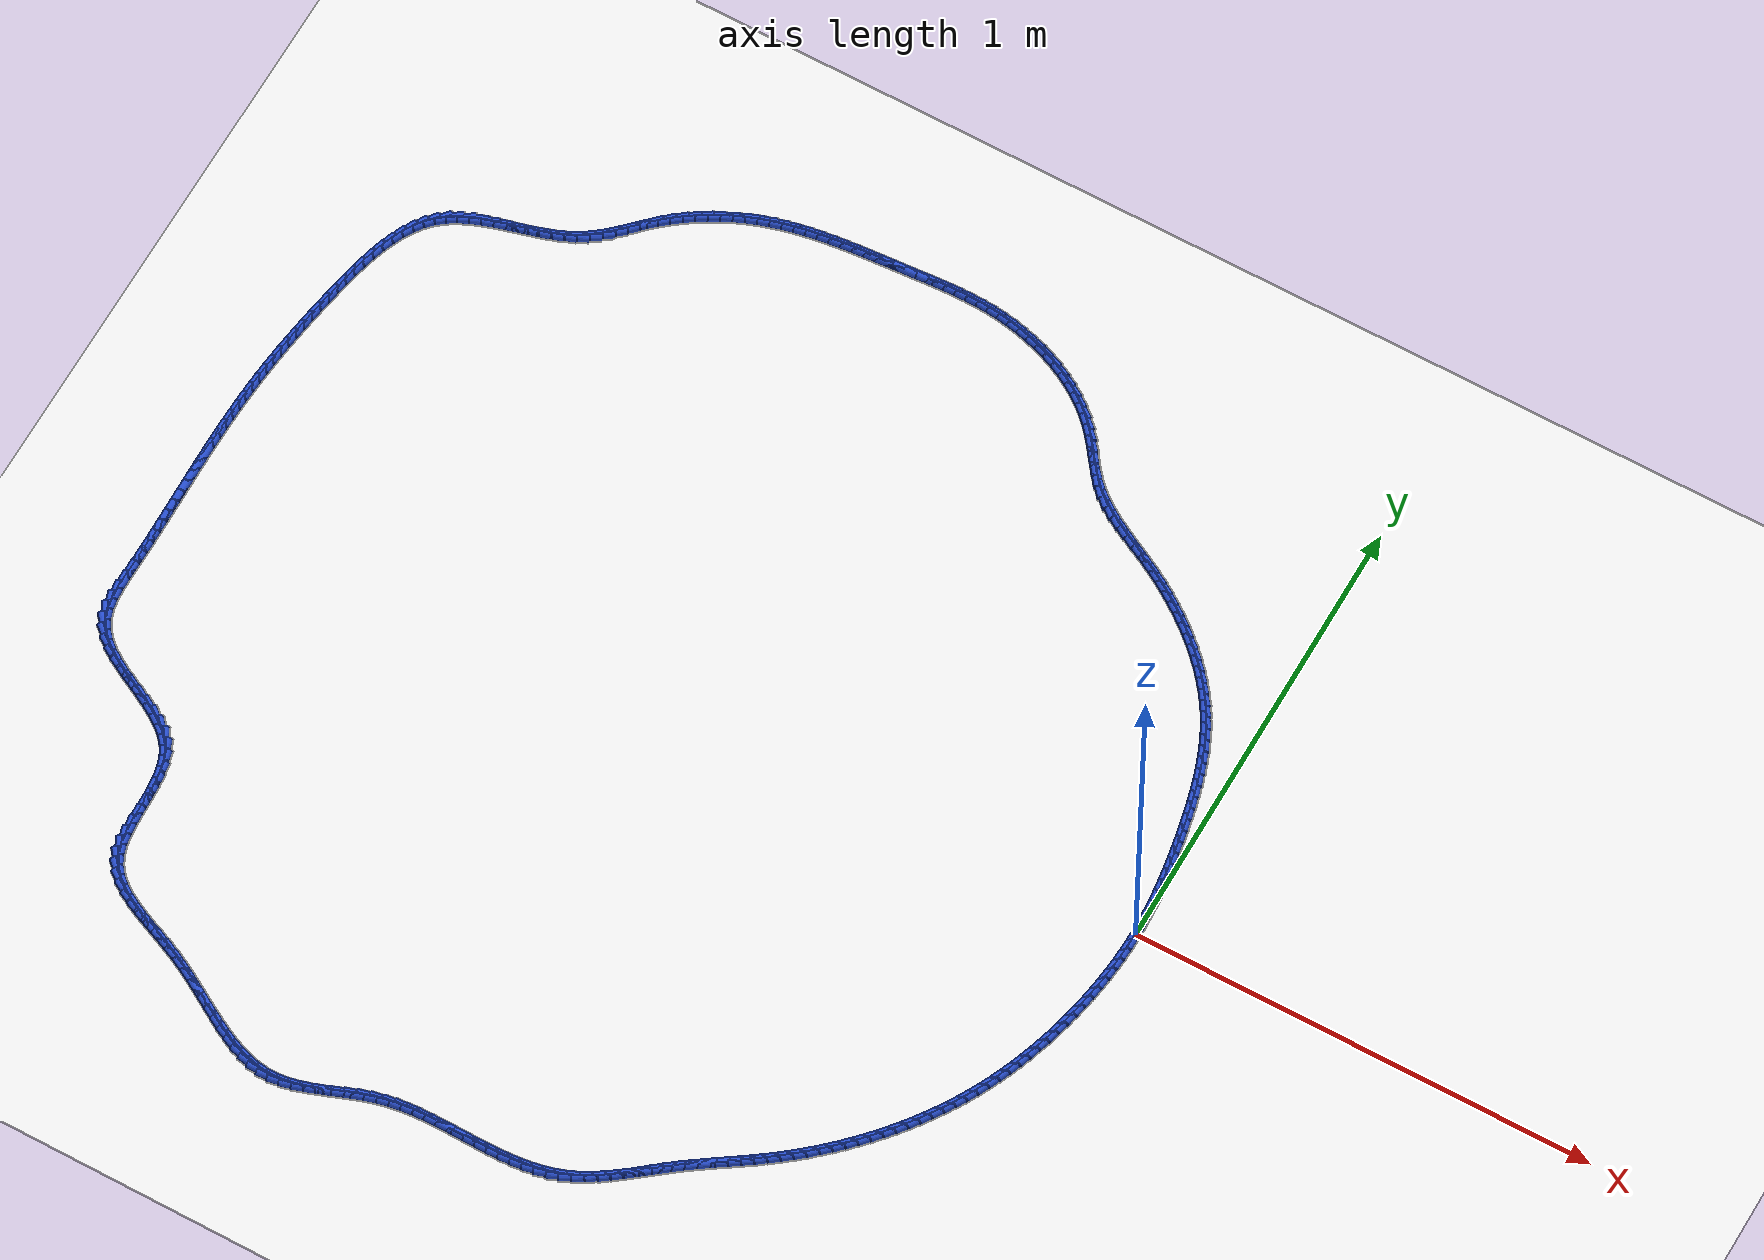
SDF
<sdf version="1.6">
 <world name="default">
  <light name="sun" type="directional">
   <pose>0 0 10 0 -0 0</pose>
   <diffuse>0.8 0.8 0.8 1</diffuse>
   <specular>0.2 0.2 0.2 1</specular>
   <attenuation>
    <range>1000</range>
    <constant>0.9</constant>
    <linear>0.01</linear>
    <quadratic>0.001</quadratic>
   </attenuation>
   <direction>-0.5 0.1 -0.9</direction>
  </light>
  <model name="ground_plane">
   <static>1</static>
   <link name="link">
    <collision name="collision">
     <geometry><plane><normal>0 0 1</normal><size>100 100</size></plane></geometry>
     <surface><friction><ode><mu>100</mu><mu2>50</mu2></ode></friction></surface>
    </collision>
    <visual name="visual">
     <cast_shadows>0</cast_shadows>
     <geometry><plane><normal>0 0 1</normal><size>100 100</size></plane></geometry>
     <material>
      <script><uri>file://media/materials/scripts/gazebo.material</uri><name>Gazebo/WhiteGlow</name></script>
     </material>
    </visual>
   </link>
  </model>
  <gravity>0 0 -9.8</gravity>
  <magnetic_field>6e-06 2.3e-05 -4.2e-05</magnetic_field>
  <atmosphere type="adiabatic"/>
  <physics name="default_physics" default="0" type="ode">
   <max_step_size>0.001</max_step_size>
   <real_time_factor>1</real_time_factor>
   <real_time_update_rate>1000</real_time_update_rate>
  </physics>
  <scene><ambient>0.4 0.4 0.4 1</ambient><background>0.7 0.7 0.7 1</background><shadows>1</shadows></scene>
  <spherical_coordinates>
   <surface_model>EARTH_WGS84</surface_model>
   <latitude_deg>0</latitude_deg>
   <longitude_deg>0</longitude_deg>
   <elevation>0</elevation>
   <heading_deg>0</heading_deg>
  </spherical_coordinates>
  <model name="line">
   <link name="link_0">
    <pose>-2.168404344971009e-18 -5.551115123125783e-17 0.01 0 1.57 -1.5480476229482256</pose>
    <collision name="collision">
     <geometry><cylinder><radius>0.01</radius><length>0.08</length></cylinder></geometry>
    </collision>
    <visual name="visual">
     <material>
      <script><name>Gazebo/Blue</name><uri>file://media/materials/scripts/gazebo.material</uri></script>
     </material>
     <geometry><cylinder><radius>0.01</radius><length>0.08</length></cylinder></geometry>
    </visual>
   </link>
   <link name="link_1">
    <pose>-0.0005697583295543874 0.025041428558802033 0.01 0 1.57 -1.5206043563029075</pose>
    <collision name="collision">
     <geometry><cylinder><radius>0.01</radius><length>0.08</length></cylinder></geometry>
    </collision>
    <visual name="visual">
     <material>
      <script><name>Gazebo/Blue</name><uri>file://media/materials/scripts/gazebo.material</uri></script>
     </material>
     <geometry><cylinder><radius>0.01</radius><length>0.08</length></cylinder></geometry>
    </visual>
   </link>
   <link name="link_2">
    <pose>-0.0018259961512323243 0.05004906848984471 0.01 0 1.57 -1.495106088449278</pose>
    <collision name="collision">
     <geometry><cylinder><radius>0.01</radius><length>0.08</length></cylinder></geometry>
    </collision>
    <visual name="visual">
     <material>
      <script><name>Gazebo/Blue</name><uri>file://media/materials/scripts/gazebo.material</uri></script>
     </material>
     <geometry><cylinder><radius>0.01</radius><length>0.08</length></cylinder></geometry>
    </visual>
   </link>
   <link name="link_3">
    <pose>-0.0037202982296581553 0.07502828964339595 0.01 0 1.57 -1.4715905317630968</pose>
    <collision name="collision">
     <geometry><cylinder><radius>0.01</radius><length>0.08</length></cylinder></geometry>
    </collision>
    <visual name="visual">
     <material>
      <script><name>Gazebo/Blue</name><uri>file://media/materials/scripts/gazebo.material</uri></script>
     </material>
     <geometry><cylinder><radius>0.01</radius><length>0.08</length></cylinder></geometry>
    </visual>
   </link>
   <link name="link_4">
    <pose>-0.0062042493294562125 0.09998446186972365 0.01 0 1.57 -1.4500802964488242</pose>
    <collision name="collision">
     <geometry><cylinder><radius>0.01</radius><length>0.08</length></cylinder></geometry>
    </collision>
    <visual name="visual">
     <material>
      <script><name>Gazebo/Blue</name><uri>file://media/materials/scripts/gazebo.material</uri></script>
     </material>
     <geometry><cylinder><radius>0.01</radius><length>0.08</length></cylinder></geometry>
    </visual>
   </link>
   <link name="link_5">
    <pose>-0.00922943421525084 0.12492295501909587 0.01 0 1.57 -1.430585549755134</pose>
    <collision name="collision">
     <geometry><cylinder><radius>0.01</radius><length>0.08</length></cylinder></geometry>
    </collision>
    <visual name="visual">
     <material>
      <script><name>Gazebo/Blue</name><uri>file://media/materials/scripts/gazebo.material</uri></script>
     </material>
     <geometry><cylinder><radius>0.01</radius><length>0.08</length></cylinder></geometry>
    </visual>
   </link>
   <link name="link_6">
    <pose>-0.012747437651666377 0.1498491389417805 0.01 0 1.57 -1.4131065929755677</pose>
    <collision name="collision">
     <geometry><cylinder><radius>0.01</radius><length>0.08</length></cylinder></geometry>
    </collision>
    <visual name="visual">
     <material>
      <script><name>Gazebo/Blue</name><uri>file://media/materials/scripts/gazebo.material</uri></script>
     </material>
     <geometry><cylinder><radius>0.01</radius><length>0.08</length></cylinder></geometry>
    </visual>
   </link>
   <link name="link_7">
    <pose>-0.01670984440332716 0.17476838348804563 0.01 0 1.57 -1.3976362624938934</pose>
    <collision name="collision">
     <geometry><cylinder><radius>0.01</radius><length>0.08</length></cylinder></geometry>
    </collision>
    <visual name="visual">
     <material>
      <script><name>Gazebo/Blue</name><uri>file://media/materials/scripts/gazebo.material</uri></script>
     </material>
     <geometry><cylinder><radius>0.01</radius><length>0.08</length></cylinder></geometry>
    </visual>
   </link>
   <link name="link_8">
    <pose>-0.021068239234857525 0.19968605850815904 0.01 0 1.57 -1.3841620944022284</pose>
    <collision name="collision">
     <geometry><cylinder><radius>0.01</radius><length>0.08</length></cylinder></geometry>
    </collision>
    <visual name="visual">
     <material>
      <script><name>Gazebo/Blue</name><uri>file://media/materials/scripts/gazebo.material</uri></script>
     </material>
     <geometry><cylinder><radius>0.01</radius><length>0.08</length></cylinder></geometry>
    </visual>
   </link>
   <link name="link_9">
    <pose>-0.025774206910881812 0.22460753385238882 0.01 0 1.57 -1.3722532291311451</pose>
    <collision name="collision">
     <geometry><cylinder><radius>0.01</radius><length>0.08</length></cylinder></geometry>
    </collision>
    <visual name="visual">
     <material>
      <script><name>Gazebo/Blue</name><uri>file://media/materials/scripts/gazebo.material</uri></script>
     </material>
     <geometry><cylinder><radius>0.01</radius><length>0.08</length></cylinder></geometry>
    </visual>
   </link>
   <link name="link_10">
    <pose>-0.030789064459453584 0.24953305191872024 0.01 0 1.57 -1.3583791332162396</pose>
    <collision name="collision">
     <geometry><cylinder><radius>0.01</radius><length>0.08</length></cylinder></geometry>
    </collision>
    <visual name="visual">
     <material>
      <script><name>Gazebo/Blue</name><uri>file://media/materials/scripts/gazebo.material</uri></script>
     </material>
     <geometry><cylinder><radius>0.01</radius><length>0.08</length></cylinder></geometry>
    </visual>
   </link>
   <link name="link_11">
    <pose>-0.0361563513686778 0.2744195361235322 0.01 0 1.57 -1.3407245242490489</pose>
    <collision name="collision">
     <geometry><cylinder><radius>0.01</radius><length>0.08</length></cylinder></geometry>
    </collision>
    <visual name="visual">
     <material>
      <script><name>Gazebo/Blue</name><uri>file://media/materials/scripts/gazebo.material</uri></script>
     </material>
     <geometry><cylinder><radius>0.01</radius><length>0.08</length></cylinder></geometry>
    </visual>
   </link>
   <link name="link_12">
    <pose>-0.04196091250709101 0.2992021481040733 0.01 0 1.57 -1.3191922778118141</pose>
    <collision name="collision">
     <geometry><cylinder><radius>0.01</radius><length>0.08</length></cylinder></geometry>
    </collision>
    <visual name="visual">
     <material>
      <script><name>Gazebo/Blue</name><uri>file://media/materials/scripts/gazebo.material</uri></script>
     </material>
     <geometry><cylinder><radius>0.01</radius><length>0.08</length></cylinder></geometry>
    </visual>
   </link>
   <link name="link_13">
    <pose>-0.04828790452591961 0.3238158852345849 0.01 0 1.57 -1.2936762294107553</pose>
    <collision name="collision">
     <geometry><cylinder><radius>0.01</radius><length>0.08</length></cylinder></geometry>
    </collision>
    <visual name="visual">
     <material>
      <script><name>Gazebo/Blue</name><uri>file://media/materials/scripts/gazebo.material</uri></script>
     </material>
     <geometry><cylinder><radius>0.01</radius><length>0.08</length></cylinder></geometry>
    </visual>
   </link>
   <link name="link_14">
    <pose>-0.05522248407638997 0.3481957448893078 0.01 0 1.57 -1.2640565944546411</pose>
    <collision name="collision">
     <geometry><cylinder><radius>0.01</radius><length>0.08</length></cylinder></geometry>
    </collision>
    <visual name="visual">
     <material>
      <script><name>Gazebo/Blue</name><uri>file://media/materials/scripts/gazebo.material</uri></script>
     </material>
     <geometry><cylinder><radius>0.01</radius><length>0.08</length></cylinder></geometry>
    </visual>
   </link>
   <link name="link_15">
    <pose>-0.06284980780972839 0.3722767244424827 0.01 0 1.57 -1.2302113667904757</pose>
    <collision name="collision">
     <geometry><cylinder><radius>0.01</radius><length>0.08</length></cylinder></geometry>
    </collision>
    <visual name="visual">
     <material>
      <script><name>Gazebo/Blue</name><uri>file://media/materials/scripts/gazebo.material</uri></script>
     </material>
     <geometry><cylinder><radius>0.01</radius><length>0.08</length></cylinder></geometry>
    </visual>
   </link>
   <link name="link_16">
    <pose>-0.07125503237716127 0.3959938212683509 0.01 0 1.57 -1.19203107122399</pose>
    <collision name="collision">
     <geometry><cylinder><radius>0.01</radius><length>0.08</length></cylinder></geometry>
    </collision>
    <visual name="visual">
     <material>
      <script><name>Gazebo/Blue</name><uri>file://media/materials/scripts/gazebo.material</uri></script>
     </material>
     <geometry><cylinder><radius>0.01</radius><length>0.08</length></cylinder></geometry>
    </visual>
   </link>
   <link name="link_17">
    <pose>-0.08052331442991495 0.41928203274115317 0.01 0 1.57 -1.1494373528756094</pose>
    <collision name="collision">
     <geometry><cylinder><radius>0.01</radius><length>0.08</length></cylinder></geometry>
    </collision>
    <visual name="visual">
     <material>
      <script><name>Gazebo/Blue</name><uri>file://media/materials/scripts/gazebo.material</uri></script>
     </material>
     <geometry><cylinder><radius>0.01</radius><length>0.08</length></cylinder></geometry>
    </visual>
   </link>
   <link name="link_18">
    <pose>-0.09073981061921578 0.44207635623513064 0.01 0 1.57 -1.1024054369803644</pose>
    <collision name="collision">
     <geometry><cylinder><radius>0.01</radius><length>0.08</length></cylinder></geometry>
    </collision>
    <visual name="visual">
     <material>
      <script><name>Gazebo/Blue</name><uri>file://media/materials/scripts/gazebo.material</uri></script>
     </material>
     <geometry><cylinder><radius>0.01</radius><length>0.08</length></cylinder></geometry>
    </visual>
   </link>
   <link name="link_19">
    <pose>-0.10198967759629016 0.4643117891245242 0.01 0 1.57 -1.0512509953364837</pose>
    <collision name="collision">
     <geometry><cylinder><radius>0.01</radius><length>0.08</length></cylinder></geometry>
    </collision>
    <visual name="visual">
     <material>
      <script><name>Gazebo/Blue</name><uri>file://media/materials/scripts/gazebo.material</uri></script>
     </material>
     <geometry><cylinder><radius>0.01</radius><length>0.08</length></cylinder></geometry>
    </visual>
   </link>
   <link name="link_20">
    <pose>-0.11435211894299326 0.4859260258240271 0.01 0 1.57 -0.9996051149049473</pose>
    <collision name="collision">
     <geometry><cylinder><radius>0.01</radius><length>0.08</length></cylinder></geometry>
    </collision>
    <visual name="visual">
     <material>
      <script><name>Gazebo/Blue</name><uri>file://media/materials/scripts/gazebo.material</uri></script>
     </material>
     <geometry><cylinder><radius>0.01</radius><length>0.08</length></cylinder></geometry>
    </visual>
   </link>
   <link name="link_21">
    <pose>-0.12782650793273184 0.5068929279014084 0.01 0 1.57 -0.9500614507901762</pose>
    <collision name="collision">
     <geometry><cylinder><radius>0.01</radius><length>0.08</length></cylinder></geometry>
    </collision>
    <visual name="visual">
     <material>
      <script><name>Gazebo/Blue</name><uri>file://media/materials/scripts/gazebo.material</uri></script>
     </material>
     <geometry><cylinder><radius>0.01</radius><length>0.08</length></cylinder></geometry>
    </visual>
   </link>
   <link name="link_22">
    <pose>-0.142355174116115 0.5272122006057975 0.01 0 1.57 -0.902707804337796</pose>
    <collision name="collision">
     <geometry><cylinder><radius>0.01</radius><length>0.08</length></cylinder></geometry>
    </collision>
    <visual name="visual">
     <material>
      <script><name>Gazebo/Blue</name><uri>file://media/materials/scripts/gazebo.material</uri></script>
     </material>
     <geometry><cylinder><radius>0.01</radius><length>0.08</length></cylinder></geometry>
    </visual>
   </link>
   <link name="link_23">
    <pose>-0.15787921327300253 0.5468841081466531 0.01 0 1.57 -0.8575364275211066</pose>
    <collision name="collision">
     <geometry><cylinder><radius>0.01</radius><length>0.08</length></cylinder></geometry>
    </collision>
    <visual name="visual">
     <material>
      <script><name>Gazebo/Blue</name><uri>file://media/materials/scripts/gazebo.material</uri></script>
     </material>
     <geometry><cylinder><radius>0.01</radius><length>0.08</length></cylinder></geometry>
    </visual>
   </link>
   <link name="link_24">
    <pose>-0.1743397211832544 0.5659089147334343 0.01 0 1.57 -0.814505635361686</pose>
    <collision name="collision">
     <geometry><cylinder><radius>0.01</radius><length>0.08</length></cylinder></geometry>
    </collision>
    <visual name="visual">
     <material>
      <script><name>Gazebo/Blue</name><uri>file://media/materials/scripts/gazebo.material</uri></script>
     </material>
     <geometry><cylinder><radius>0.01</radius><length>0.08</length></cylinder></geometry>
    </visual>
   </link>
   <link name="link_25">
    <pose>-0.19167779362673035 0.5842868845756001 0.01 0 1.57 -0.7735470155147254</pose>
    <collision name="collision">
     <geometry><cylinder><radius>0.01</radius><length>0.08</length></cylinder></geometry>
    </collision>
    <visual name="visual">
     <material>
      <script><name>Gazebo/Blue</name><uri>file://media/materials/scripts/gazebo.material</uri></script>
     </material>
     <geometry><cylinder><radius>0.01</radius><length>0.08</length></cylinder></geometry>
    </visual>
   </link>
   <link name="link_26">
    <pose>-0.2098345263832903 0.6020182818826095 0.01 0 1.57 -0.7345719860970964</pose>
    <collision name="collision">
     <geometry><cylinder><radius>0.01</radius><length>0.08</length></cylinder></geometry>
    </collision>
    <visual name="visual">
     <material>
      <script><name>Gazebo/Blue</name><uri>file://media/materials/scripts/gazebo.material</uri></script>
     </material>
     <geometry><cylinder><radius>0.01</radius><length>0.08</length></cylinder></geometry>
    </visual>
   </link>
   <link name="link_27">
    <pose>-0.22875101523279415 0.6191033708639219 0.01 0 1.57 -0.6974774768604937</pose>
    <collision name="collision">
     <geometry><cylinder><radius>0.01</radius><length>0.08</length></cylinder></geometry>
    </collision>
    <visual name="visual">
     <material>
      <script><name>Gazebo/Blue</name><uri>file://media/materials/scripts/gazebo.material</uri></script>
     </material>
     <geometry><cylinder><radius>0.01</radius><length>0.08</length></cylinder></geometry>
    </visual>
   </link>
   <link name="link_28">
    <pose>-0.2483683559551018 0.6355424157289957 0.01 0 1.57 -0.662150648787534</pose>
    <collision name="collision">
     <geometry><cylinder><radius>0.01</radius><length>0.08</length></cylinder></geometry>
    </collision>
    <visual name="visual">
     <material>
      <script><name>Gazebo/Blue</name><uri>file://media/materials/scripts/gazebo.material</uri></script>
     </material>
     <geometry><cylinder><radius>0.01</radius><length>0.08</length></cylinder></geometry>
    </visual>
   </link>
   <link name="link_29">
    <pose>-0.26862764433007297 0.6513356806872904 0.01 0 1.57 -0.6284726643645151</pose>
    <collision name="collision">
     <geometry><cylinder><radius>0.01</radius><length>0.08</length></cylinder></geometry>
    </collision>
    <visual name="visual">
     <material>
      <script><name>Gazebo/Blue</name><uri>file://media/materials/scripts/gazebo.material</uri></script>
     </material>
     <geometry><cylinder><radius>0.01</radius><length>0.08</length></cylinder></geometry>
    </visual>
   </link>
   <link name="link_30">
    <pose>-0.28946997613756764 0.6664834299482647 0.01 0 1.57 -0.5963215803113437</pose>
    <collision name="collision">
     <geometry><cylinder><radius>0.01</radius><length>0.08</length></cylinder></geometry>
    </collision>
    <visual name="visual">
     <material>
      <script><name>Gazebo/Blue</name><uri>file://media/materials/scripts/gazebo.material</uri></script>
     </material>
     <geometry><cylinder><radius>0.01</radius><length>0.08</length></cylinder></geometry>
    </visual>
   </link>
   <link name="link_31">
    <pose>-0.3108364471574455 0.6809859277213778 0.01 0 1.57 -0.5655744646744059</pose>
    <collision name="collision">
     <geometry><cylinder><radius>0.01</radius><length>0.08</length></cylinder></geometry>
    </collision>
    <visual name="visual">
     <material>
      <script><name>Gazebo/Blue</name><uri>file://media/materials/scripts/gazebo.material</uri></script>
     </material>
     <geometry><cylinder><radius>0.01</radius><length>0.08</length></cylinder></geometry>
    </visual>
   </link>
   <link name="link_32">
    <pose>-0.3326681531695667 0.6948434382160888 0.01 0 1.57 -0.5361088494481401</pose>
    <collision name="collision">
     <geometry><cylinder><radius>0.01</radius><length>0.08</length></cylinder></geometry>
    </collision>
    <visual name="visual">
     <material>
      <script><name>Gazebo/Blue</name><uri>file://media/materials/scripts/gazebo.material</uri></script>
     </material>
     <geometry><cylinder><radius>0.01</radius><length>0.08</length></cylinder></geometry>
    </visual>
   </link>
   <link name="link_33">
    <pose>-0.3549061899537911 0.7080562256418568 0.01 0 1.57 -0.5080522299276821</pose>
    <collision name="collision">
     <geometry><cylinder><radius>0.01</radius><length>0.08</length></cylinder></geometry>
    </collision>
    <visual name="visual">
     <material>
      <script><name>Gazebo/Blue</name><uri>file://media/materials/scripts/gazebo.material</uri></script>
     </material>
     <geometry><cylinder><radius>0.01</radius><length>0.08</length></cylinder></geometry>
    </visual>
   </link>
   <link name="link_34">
    <pose>-0.377488407385569 0.7206301014757267 0.01 0 1.57 -0.48785186965999316</pose>
    <collision name="collision">
     <geometry><cylinder><radius>0.01</radius><length>0.08</length></cylinder></geometry>
    </collision>
    <visual name="visual">
     <material>
      <script><name>Gazebo/Blue</name><uri>file://media/materials/scripts/gazebo.material</uri></script>
     </material>
     <geometry><cylinder><radius>0.01</radius><length>0.08</length></cylinder></geometry>
    </visual>
   </link>
   <link name="link_35">
    <pose>-0.40026704934569296 0.7327171782866542 0.01 0 1.57 -0.48254880784526105</pose>
    <collision name="collision">
     <geometry><cylinder><radius>0.01</radius><length>0.08</length></cylinder></geometry>
    </collision>
    <visual name="visual">
     <material>
      <script><name>Gazebo/Blue</name><uri>file://media/materials/scripts/gazebo.material</uri></script>
     </material>
     <geometry><cylinder><radius>0.01</radius><length>0.08</length></cylinder></geometry>
    </visual>
   </link>
   <link name="link_36">
    <pose>-0.42300218854203875 0.7446270896594379 0.01 0 1.57 -0.4926712706315808</pose>
    <collision name="collision">
     <geometry><cylinder><radius>0.01</radius><length>0.08</length></cylinder></geometry>
    </collision>
    <visual name="visual">
     <material>
      <script><name>Gazebo/Blue</name><uri>file://media/materials/scripts/gazebo.material</uri></script>
     </material>
     <geometry><cylinder><radius>0.01</radius><length>0.08</length></cylinder></geometry>
    </visual>
   </link>
   <link name="link_37">
    <pose>-0.44544933649459584 0.7566772642727891 0.01 0 1.57 -0.5186368232506255</pose>
    <collision name="collision">
     <geometry><cylinder><radius>0.01</radius><length>0.08</length></cylinder></geometry>
    </collision>
    <visual name="visual">
     <material>
      <script><name>Gazebo/Blue</name><uri>file://media/materials/scripts/gazebo.material</uri></script>
     </material>
     <geometry><cylinder><radius>0.01</radius><length>0.08</length></cylinder></geometry>
    </visual>
   </link>
   <link name="link_38">
    <pose>-0.46736400472335476 0.7691851308054202 0.01 0 1.57 -0.5610424379605093</pose>
    <collision name="collision">
     <geometry><cylinder><radius>0.01</radius><length>0.08</length></cylinder></geometry>
    </collision>
    <visual name="visual">
     <material>
      <script><name>Gazebo/Blue</name><uri>file://media/materials/scripts/gazebo.material</uri></script>
     </material>
     <geometry><cylinder><radius>0.01</radius><length>0.08</length></cylinder></geometry>
    </visual>
   </link>
   <link name="link_39">
    <pose>-0.4885017047483057 0.7824681179360428 0.01 0 1.57 -0.6204729936003492</pose>
    <collision name="collision">
     <geometry><cylinder><radius>0.01</radius><length>0.08</length></cylinder></geometry>
    </collision>
    <visual name="visual">
     <material>
      <script><name>Gazebo/Blue</name><uri>file://media/materials/scripts/gazebo.material</uri></script>
     </material>
     <geometry><cylinder><radius>0.01</radius><length>0.08</length></cylinder></geometry>
    </visual>
   </link>
   <link name="link_40">
    <pose>-0.5086179480894385 0.7968436543433686 0.01 0 1.57 -0.6971420461137727</pose>
    <collision name="collision">
     <geometry><cylinder><radius>0.01</radius><length>0.08</length></cylinder></geometry>
    </collision>
    <visual name="visual">
     <material>
      <script><name>Gazebo/Blue</name><uri>file://media/materials/scripts/gazebo.material</uri></script>
     </material>
     <geometry><cylinder><radius>0.01</radius><length>0.08</length></cylinder></geometry>
    </visual>
   </link>
   <link name="link_41">
    <pose>-0.5274682462667437 0.8126291687061098 0.01 0 1.57 -0.7883861440349522</pose>
    <collision name="collision">
     <geometry><cylinder><radius>0.01</radius><length>0.08</length></cylinder></geometry>
    </collision>
    <visual name="visual">
     <material>
      <script><name>Gazebo/Blue</name><uri>file://media/materials/scripts/gazebo.material</uri></script>
     </material>
     <geometry><cylinder><radius>0.01</radius><length>0.08</length></cylinder></geometry>
    </visual>
   </link>
   <link name="link_42">
    <pose>-0.5448404984559726 0.8301055482420612 0.01 0 1.57 -0.8661707938594106</pose>
    <collision name="collision">
     <geometry><cylinder><radius>0.01</radius><length>0.08</length></cylinder></geometry>
    </collision>
    <visual name="visual">
     <material>
      <script><name>Gazebo/Blue</name><uri>file://media/materials/scripts/gazebo.material</uri></script>
     </material>
     <geometry><cylinder><radius>0.01</radius><length>0.08</length></cylinder></geometry>
    </visual>
   </link>
   <link name="link_43">
    <pose>-0.5609580778750421 0.8490623553936387 0.01 0 1.57 -0.9116480694812913</pose>
    <collision name="collision">
     <geometry><cylinder><radius>0.01</radius><length>0.08</length></cylinder></geometry>
    </collision>
    <visual name="visual">
     <material>
      <script><name>Gazebo/Blue</name><uri>file://media/materials/scripts/gazebo.material</uri></script>
     </material>
     <geometry><cylinder><radius>0.01</radius><length>0.08</length></cylinder></geometry>
    </visual>
   </link>
   <link name="link_44">
    <pose>-0.5763561067219904 0.86893742096646 0.01 0 1.57 -0.9256283333738456</pose>
    <collision name="collision">
     <geometry><cylinder><radius>0.01</radius><length>0.08</length></cylinder></geometry>
    </collision>
    <visual name="visual">
     <material>
      <script><name>Gazebo/Blue</name><uri>file://media/materials/scripts/gazebo.material</uri></script>
     </material>
     <geometry><cylinder><radius>0.01</radius><length>0.08</length></cylinder></geometry>
    </visual>
   </link>
   <link name="link_45">
    <pose>-0.5915764800064579 0.8891609343229893 0.01 0 1.57 -0.9089006810155099</pose>
    <collision name="collision">
     <geometry><cylinder><radius>0.01</radius><length>0.08</length></cylinder></geometry>
    </collision>
    <visual name="visual">
     <material>
      <script><name>Gazebo/Blue</name><uri>file://media/materials/scripts/gazebo.material</uri></script>
     </material>
     <geometry><cylinder><radius>0.01</radius><length>0.08</length></cylinder></geometry>
    </visual>
   </link>
   <link name="link_46">
    <pose>-0.6071610927380837 0.9091630848256897 0.01 0 1.57 -0.8614447812594681</pose>
    <collision name="collision">
     <geometry><cylinder><radius>0.01</radius><length>0.08</length></cylinder></geometry>
    </collision>
    <visual name="visual">
     <material>
      <script><name>Gazebo/Blue</name><uri>file://media/materials/scripts/gazebo.material</uri></script>
     </material>
     <geometry><cylinder><radius>0.01</radius><length>0.08</length></cylinder></geometry>
    </visual>
   </link>
   <link name="link_47">
    <pose>-0.6236518338899116 0.9283740671181507 0.01 0 1.57 -0.7893991667646886</pose>
    <collision name="collision">
     <geometry><cylinder><radius>0.01</radius><length>0.08</length></cylinder></geometry>
    </collision>
    <visual name="visual">
     <material>
      <script><name>Gazebo/Blue</name><uri>file://media/materials/scripts/gazebo.material</uri></script>
     </material>
     <geometry><cylinder><radius>0.01</radius><length>0.08</length></cylinder></geometry>
    </visual>
   </link>
   <link name="link_48">
    <pose>-0.6414669135044594 0.9463322765463587 0.01 0 1.57 -0.7159673168174842</pose>
    <collision name="collision">
     <geometry><cylinder><radius>0.01</radius><length>0.08</length></cylinder></geometry>
    </collision>
    <visual name="visual">
     <material>
      <script><name>Gazebo/Blue</name><uri>file://media/materials/scripts/gazebo.material</uri></script>
     </material>
     <geometry><cylinder><radius>0.01</radius><length>0.08</length></cylinder></geometry>
    </visual>
   </link>
   <link name="link_49">
    <pose>-0.6605829537223217 0.9629624323107783 0.01 0 1.57 -0.6463857907514414</pose>
    <collision name="collision">
     <geometry><cylinder><radius>0.01</radius><length>0.08</length></cylinder></geometry>
    </collision>
    <visual name="visual">
     <material>
      <script><name>Gazebo/Blue</name><uri>file://media/materials/scripts/gazebo.material</uri></script>
     </material>
     <geometry><cylinder><radius>0.01</radius><length>0.08</length></cylinder></geometry>
    </visual>
   </link>
   <link name="link_50">
    <pose>-0.6808780624688578 0.9782754389244361 0.01 0 1.57 -0.5805705512661311</pose>
    <collision name="collision">
     <geometry><cylinder><radius>0.01</radius><length>0.08</length></cylinder></geometry>
    </collision>
    <visual name="visual">
     <material>
      <script><name>Gazebo/Blue</name><uri>file://media/materials/scripts/gazebo.material</uri></script>
     </material>
     <geometry><cylinder><radius>0.01</radius><length>0.08</length></cylinder></geometry>
    </visual>
   </link>
   <link name="link_51">
    <pose>-0.7022303476694266 0.9922822009003589 0.01 0 1.57 -0.518322724445288</pose>
    <collision name="collision">
     <geometry><cylinder><radius>0.01</radius><length>0.08</length></cylinder></geometry>
    </collision>
    <visual name="visual">
     <material>
      <script><name>Gazebo/Blue</name><uri>file://media/materials/scripts/gazebo.material</uri></script>
     </material>
     <geometry><cylinder><radius>0.01</radius><length>0.08</length></cylinder></geometry>
    </visual>
   </link>
   <link name="link_52">
    <pose>-0.7245179172493874 1.0049936227515732 0.01 0 1.57 -0.45936177584268767</pose>
    <collision name="collision">
     <geometry><cylinder><radius>0.01</radius><length>0.08</length></cylinder></geometry>
    </collision>
    <visual name="visual">
     <material>
      <script><name>Gazebo/Blue</name><uri>file://media/materials/scripts/gazebo.material</uri></script>
     </material>
     <geometry><cylinder><radius>0.01</radius><length>0.08</length></cylinder></geometry>
    </visual>
   </link>
   <link name="link_53">
    <pose>-0.7476188791340993 1.016420608991105 0.01 0 1.57 -0.4033527587623091</pose>
    <collision name="collision">
     <geometry><cylinder><radius>0.01</radius><length>0.08</length></cylinder></geometry>
    </collision>
    <visual name="visual">
     <material>
      <script><name>Gazebo/Blue</name><uri>file://media/materials/scripts/gazebo.material</uri></script>
     </material>
     <geometry><cylinder><radius>0.01</radius><length>0.08</length></cylinder></geometry>
    </visual>
   </link>
   <link name="link_54">
    <pose>-0.7714113412489214 1.0265740641319814 0.01 0 1.57 -0.34992678481494555</pose>
    <collision name="collision">
     <geometry><cylinder><radius>0.01</radius><length>0.08</length></cylinder></geometry>
    </collision>
    <visual name="visual">
     <material>
      <script><name>Gazebo/Blue</name><uri>file://media/materials/scripts/gazebo.material</uri></script>
     </material>
     <geometry><cylinder><radius>0.01</radius><length>0.08</length></cylinder></geometry>
    </visual>
   </link>
   <link name="link_55">
    <pose>-0.7957734115192124 1.0354648926872283 0.01 0 1.57 -0.29869502922283847</pose>
    <collision name="collision">
     <geometry><cylinder><radius>0.01</radius><length>0.08</length></cylinder></geometry>
    </collision>
    <visual name="visual">
     <material>
      <script><name>Gazebo/Blue</name><uri>file://media/materials/scripts/gazebo.material</uri></script>
     </material>
     <geometry><cylinder><radius>0.01</radius><length>0.08</length></cylinder></geometry>
    </visual>
   </link>
   <link name="link_56">
    <pose>-0.8205831978703317 1.0431039991698727 0.01 0 1.57 -0.24925713159833776</pose>
    <collision name="collision">
     <geometry><cylinder><radius>0.01</radius><length>0.08</length></cylinder></geometry>
    </collision>
    <visual name="visual">
     <material>
      <script><name>Gazebo/Blue</name><uri>file://media/materials/scripts/gazebo.material</uri></script>
     </material>
     <geometry><cylinder><radius>0.01</radius><length>0.08</length></cylinder></geometry>
    </visual>
   </link>
   <link name="link_57">
    <pose>-0.8457188082276381 1.0495022880929408 0.01 0 1.57 -0.20120499011365428</pose>
    <collision name="collision">
     <geometry><cylinder><radius>0.01</radius><length>0.08</length></cylinder></geometry>
    </collision>
    <visual name="visual">
     <material>
      <script><name>Gazebo/Blue</name><uri>file://media/materials/scripts/gazebo.material</uri></script>
     </material>
     <geometry><cylinder><radius>0.01</radius><length>0.08</length></cylinder></geometry>
    </visual>
   </link>
   <link name="link_58">
    <pose>-0.871058350516491 1.0546706639694592 0.01 0 1.57 -0.1541228547095058</pose>
    <collision name="collision">
     <geometry><cylinder><radius>0.01</radius><length>0.08</length></cylinder></geometry>
    </collision>
    <visual name="visual">
     <material>
      <script><name>Gazebo/Blue</name><uri>file://media/materials/scripts/gazebo.material</uri></script>
     </material>
     <geometry><cylinder><radius>0.01</radius><length>0.08</length></cylinder></geometry>
    </visual>
   </link>
   <link name="link_59">
    <pose>-0.8964799326622497 1.0586200313124545 0.01 0 1.57 -0.10758885201200187</pose>
    <collision name="collision">
     <geometry><cylinder><radius>0.01</radius><length>0.08</length></cylinder></geometry>
    </collision>
    <visual name="visual">
     <material>
      <script><name>Gazebo/Blue</name><uri>file://media/materials/scripts/gazebo.material</uri></script>
     </material>
     <geometry><cylinder><radius>0.01</radius><length>0.08</length></cylinder></geometry>
    </visual>
   </link>
   <link name="link_60">
    <pose>-0.9218617835682248 1.0613614212109321 0.01 0 1.57 -0.06273153461965056</pose>
    <collision name="collision">
     <geometry><cylinder><radius>0.01</radius><length>0.08</length></cylinder></geometry>
    </collision>
    <visual name="visual">
     <material>
      <script><name>Gazebo/Blue</name><uri>file://media/materials/scripts/gazebo.material</uri></script>
     </material>
     <geometry><cylinder><radius>0.01</radius><length>0.08</length></cylinder></geometry>
    </visual>
   </link>
   <link name="link_61">
    <pose>-0.9471225468612412 1.062948149592764 0.01 0 1.57 -0.02339901956416298</pose>
    <collision name="collision">
     <geometry><cylinder><radius>0.01</radius><length>0.08</length></cylinder></geometry>
    </collision>
    <visual name="visual">
     <material>
      <script><name>Gazebo/Blue</name><uri>file://media/materials/scripts/gazebo.material</uri></script>
     </material>
     <geometry><cylinder><radius>0.01</radius><length>0.08</length></cylinder></geometry>
    </visual>
   </link>
   <link name="link_62">
    <pose>-0.9722796708654999 1.0635369090848177 0.01 0 1.57 0.00944782095628531</pose>
    <collision name="collision">
     <geometry><cylinder><radius>0.01</radius><length>0.08</length></cylinder></geometry>
    </collision>
    <visual name="visual">
     <material>
      <script><name>Gazebo/Blue</name><uri>file://media/materials/scripts/gazebo.material</uri></script>
     </material>
     <geometry><cylinder><radius>0.01</radius><length>0.08</length></cylinder></geometry>
    </visual>
   </link>
   <link name="link_63">
    <pose>-0.9973654222455579 1.0632998963451596 0.01 0 1.57 0.0355422155402699</pose>
    <collision name="collision">
     <geometry><cylinder><radius>0.01</radius><length>0.08</length></cylinder></geometry>
    </collision>
    <visual name="visual">
     <material>
      <script><name>Gazebo/Blue</name><uri>file://media/materials/scripts/gazebo.material</uri></script>
     </material>
     <geometry><cylinder><radius>0.01</radius><length>0.08</length></cylinder></geometry>
    </visual>
   </link>
   <link name="link_64">
    <pose>-1.0224120676659734 1.0624093080318564 0.01 0 1.57 0.05473671644555952</pose>
    <collision name="collision">
     <geometry><cylinder><radius>0.01</radius><length>0.08</length></cylinder></geometry>
    </collision>
    <visual name="visual">
     <material>
      <script><name>Gazebo/Blue</name><uri>file://media/materials/scripts/gazebo.material</uri></script>
     </material>
     <geometry><cylinder><radius>0.01</radius><length>0.08</length></cylinder></geometry>
    </visual>
   </link>
   <link name="link_65">
    <pose>-1.0474518737913037 1.061037340802974 0.01 0 1.57 0.06697066584915144</pose>
    <collision name="collision">
     <geometry><cylinder><radius>0.01</radius><length>0.08</length></cylinder></geometry>
    </collision>
    <visual name="visual">
     <material>
      <script><name>Gazebo/Blue</name><uri>file://media/materials/scripts/gazebo.material</uri></script>
     </material>
     <geometry><cylinder><radius>0.01</radius><length>0.08</length></cylinder></geometry>
    </visual>
   </link>
   <link name="link_66">
    <pose>-1.0725171072861057 1.0593561913165797 0.01 0 1.57 0.0722436089262853</pose>
    <collision name="collision">
     <geometry><cylinder><radius>0.01</radius><length>0.08</length></cylinder></geometry>
    </collision>
    <visual name="visual">
     <material>
      <script><name>Gazebo/Blue</name><uri>file://media/materials/scripts/gazebo.material</uri></script>
     </material>
     <geometry><cylinder><radius>0.01</radius><length>0.08</length></cylinder></geometry>
    </visual>
   </link>
   <link name="link_67">
    <pose>-1.0976400348149369 1.0575380562307388 0.01 0 1.57 0.07104448228106962</pose>
    <collision name="collision">
     <geometry><cylinder><radius>0.01</radius><length>0.08</length></cylinder></geometry>
    </collision>
    <visual name="visual">
     <material>
      <script><name>Gazebo/Blue</name><uri>file://media/materials/scripts/gazebo.material</uri></script>
     </material>
     <geometry><cylinder><radius>0.01</radius><length>0.08</length></cylinder></geometry>
    </visual>
   </link>
   <link name="link_68">
    <pose>-1.1228500907721137 1.0557440014522426 0.01 0 1.57 0.06941004793169686</pose>
    <collision name="collision">
     <geometry><cylinder><radius>0.01</radius><length>0.08</length></cylinder></geometry>
    </collision>
    <visual name="visual">
     <material>
      <script><name>Gazebo/Blue</name><uri>file://media/materials/scripts/gazebo.material</uri></script>
     </material>
     <geometry><cylinder><radius>0.01</radius><length>0.08</length></cylinder></geometry>
    </visual>
   </link>
   <link name="link_69">
    <pose>-1.148138744328165 1.0539858905070938 0.01 0 1.57 0.0716015597323159</pose>
    <collision name="collision">
     <geometry><cylinder><radius>0.01</radius><length>0.08</length></cylinder></geometry>
    </collision>
    <visual name="visual">
     <material>
      <script><name>Gazebo/Blue</name><uri>file://media/materials/scripts/gazebo.material</uri></script>
     </material>
     <geometry><cylinder><radius>0.01</radius><length>0.08</length></cylinder></geometry>
    </visual>
   </link>
   <link name="link_70">
    <pose>-1.1734703437595058 1.0521690024851331 0.01 0 1.57 0.07769731624842807</pose>
    <collision name="collision">
     <geometry><cylinder><radius>0.01</radius><length>0.08</length></cylinder></geometry>
    </collision>
    <visual name="visual">
     <material>
      <script><name>Gazebo/Blue</name><uri>file://media/materials/scripts/gazebo.material</uri></script>
     </material>
     <geometry><cylinder><radius>0.01</radius><length>0.08</length></cylinder></geometry>
    </visual>
   </link>
   <link name="link_71">
    <pose>-1.198808651156051 1.0501963127779042 0.01 0 1.57 0.08770894665830445</pose>
    <collision name="collision">
     <geometry><cylinder><radius>0.01</radius><length>0.08</length></cylinder></geometry>
    </collision>
    <visual name="visual">
     <material>
      <script><name>Gazebo/Blue</name><uri>file://media/materials/scripts/gazebo.material</uri></script>
     </material>
     <geometry><cylinder><radius>0.01</radius><length>0.08</length></cylinder></geometry>
    </visual>
   </link>
   <link name="link_72">
    <pose>-1.2241174286077159 1.047970796776952 0.01 0 1.57 0.10167119293186301</pose>
    <collision name="collision">
     <geometry><cylinder><radius>0.01</radius><length>0.08</length></cylinder></geometry>
    </collision>
    <visual name="visual">
     <material>
      <script><name>Gazebo/Blue</name><uri>file://media/materials/scripts/gazebo.material</uri></script>
     </material>
     <geometry><cylinder><radius>0.01</radius><length>0.08</length></cylinder></geometry>
    </visual>
   </link>
   <link name="link_73">
    <pose>-1.2493604382044161 1.0453954298738213 0.01 0 1.57 0.11963760003585429</pose>
    <collision name="collision">
     <geometry><cylinder><radius>0.01</radius><length>0.08</length></cylinder></geometry>
    </collision>
    <visual name="visual">
     <material>
      <script><name>Gazebo/Blue</name><uri>file://media/materials/scripts/gazebo.material</uri></script>
     </material>
     <geometry><cylinder><radius>0.01</radius><length>0.08</length></cylinder></geometry>
    </visual>
   </link>
   <link name="link_74">
    <pose>-1.274501442036066 1.0423731874600561 0.01 0 1.57 0.14167440251892457</pose>
    <collision name="collision">
     <geometry><cylinder><radius>0.01</radius><length>0.08</length></cylinder></geometry>
    </collision>
    <visual name="visual">
     <material>
      <script><name>Gazebo/Blue</name><uri>file://media/materials/scripts/gazebo.material</uri></script>
     </material>
     <geometry><cylinder><radius>0.01</radius><length>0.08</length></cylinder></geometry>
    </visual>
   </link>
   <link name="link_75">
    <pose>-1.2995042021925802 1.0388070449272009 0.01 0 1.57 0.16785224706669022</pose>
    <collision name="collision">
     <geometry><cylinder><radius>0.01</radius><length>0.08</length></cylinder></geometry>
    </collision>
    <visual name="visual">
     <material>
      <script><name>Gazebo/Blue</name><uri>file://media/materials/scripts/gazebo.material</uri></script>
     </material>
     <geometry><cylinder><radius>0.01</radius><length>0.08</length></cylinder></geometry>
    </visual>
   </link>
   <link name="link_76">
    <pose>-1.3243324807638752 1.0345999776668007 0.01 0 1.57 0.1982353748869808</pose>
    <collision name="collision">
     <geometry><cylinder><radius>0.01</radius><length>0.08</length></cylinder></geometry>
    </collision>
    <visual name="visual">
     <material>
      <script><name>Gazebo/Blue</name><uri>file://media/materials/scripts/gazebo.material</uri></script>
     </material>
     <geometry><cylinder><radius>0.01</radius><length>0.08</length></cylinder></geometry>
    </visual>
   </link>
   <link name="link_77">
    <pose>-1.3489500398398646 1.029654961070399 0.01 0 1.57 0.23286797814396953</pose>
    <collision name="collision">
     <geometry><cylinder><radius>0.01</radius><length>0.08</length></cylinder></geometry>
    </collision>
    <visual name="visual">
     <material>
      <script><name>Gazebo/Blue</name><uri>file://media/materials/scripts/gazebo.material</uri></script>
     </material>
     <geometry><cylinder><radius>0.01</radius><length>0.08</length></cylinder></geometry>
    </visual>
   </link>
   <link name="link_78">
    <pose>-1.3733206415104644 1.023874970529541 0.01 0 1.57 0.27175769354264806</pose>
    <collision name="collision">
     <geometry><cylinder><radius>0.01</radius><length>0.08</length></cylinder></geometry>
    </collision>
    <visual name="visual">
     <material>
      <script><name>Gazebo/Blue</name><uri>file://media/materials/scripts/gazebo.material</uri></script>
     </material>
     <geometry><cylinder><radius>0.01</radius><length>0.08</length></cylinder></geometry>
    </visual>
   </link>
   <link name="link_79">
    <pose>-1.3974080478655895 1.0171629814357708 0.01 0 1.57 0.31485665595257356</pose>
    <collision name="collision">
     <geometry><cylinder><radius>0.01</radius><length>0.08</length></cylinder></geometry>
    </collision>
    <visual name="visual">
     <material>
      <script><name>Gazebo/Blue</name><uri>file://media/materials/scripts/gazebo.material</uri></script>
     </material>
     <geometry><cylinder><radius>0.01</radius><length>0.08</length></cylinder></geometry>
    </visual>
   </link>
   <link name="link_80">
    <pose>-1.4211760209951538 1.0094219691806328 0.01 0 1.57 0.3620290250035916</pose>
    <collision name="collision">
     <geometry><cylinder><radius>0.01</radius><length>0.08</length></cylinder></geometry>
    </collision>
    <visual name="visual">
     <material>
      <script><name>Gazebo/Blue</name><uri>file://media/materials/scripts/gazebo.material</uri></script>
     </material>
     <geometry><cylinder><radius>0.01</radius><length>0.08</length></cylinder></geometry>
    </visual>
   </link>
   <link name="link_81">
    <pose>-1.4445882470236788 1.0005552646984386 0.01 0 1.57 0.4116936275311137</pose>
    <collision name="collision">
     <geometry><cylinder><radius>0.01</radius><length>0.08</length></cylinder></geometry>
    </collision>
    <visual name="visual">
     <material>
      <script><name>Gazebo/Blue</name><uri>file://media/materials/scripts/gazebo.material</uri></script>
     </material>
     <geometry><cylinder><radius>0.01</radius><length>0.08</length></cylinder></geometry>
    </visual>
   </link>
   <link name="link_82">
    <pose>-1.4675995996724436 0.9905074438376876 0.01 0 1.57 0.4611957048522582</pose>
    <collision name="collision">
     <geometry><cylinder><radius>0.01</radius><length>0.08</length></cylinder></geometry>
    </collision>
    <visual name="visual">
     <material>
      <script><name>Gazebo/Blue</name><uri>file://media/materials/scripts/gazebo.material</uri></script>
     </material>
     <geometry><cylinder><radius>0.01</radius><length>0.08</length></cylinder></geometry>
    </visual>
   </link>
   <link name="link_83">
    <pose>-1.4901480380280288 0.9793022484403023 0.01 0 1.57 0.5104117197355084</pose>
    <collision name="collision">
     <geometry><cylinder><radius>0.01</radius><length>0.08</length></cylinder></geometry>
    </collision>
    <visual name="visual">
     <material>
      <script><name>Gazebo/Blue</name><uri>file://media/materials/scripts/gazebo.material</uri></script>
     </material>
     <geometry><cylinder><radius>0.01</radius><length>0.08</length></cylinder></geometry>
    </visual>
   </link>
   <link name="link_84">
    <pose>-1.5121696054677067 0.966972386491007 0.01 0 1.57 0.5595251586221003</pose>
    <collision name="collision">
     <geometry><cylinder><radius>0.01</radius><length>0.08</length></cylinder></geometry>
    </collision>
    <visual name="visual">
     <material>
      <script><name>Gazebo/Blue</name><uri>file://media/materials/scripts/gazebo.material</uri></script>
     </material>
     <geometry><cylinder><radius>0.01</radius><length>0.08</length></cylinder></geometry>
    </visual>
   </link>
   <link name="link_85">
    <pose>-1.5336003453687537 0.9535505659745285 0.01 0 1.57 0.6087171516924712</pose>
    <collision name="collision">
     <geometry><cylinder><radius>0.01</radius><length>0.08</length></cylinder></geometry>
    </collision>
    <visual name="visual">
     <material>
      <script><name>Gazebo/Blue</name><uri>file://media/materials/scripts/gazebo.material</uri></script>
     </material>
     <geometry><cylinder><radius>0.01</radius><length>0.08</length></cylinder></geometry>
    </visual>
   </link>
   <link name="link_86">
    <pose>-1.5543763011084424 0.9390694948755918 0.01 0 1.57 0.6581650278645419</pose>
    <collision name="collision">
     <geometry><cylinder><radius>0.01</radius><length>0.08</length></cylinder></geometry>
    </collision>
    <visual name="visual">
     <material>
      <script><name>Gazebo/Blue</name><uri>file://media/materials/scripts/gazebo.material</uri></script>
     </material>
     <geometry><cylinder><radius>0.01</radius><length>0.08</length></cylinder></geometry>
    </visual>
   </link>
   <link name="link_87">
    <pose>-1.5744335160640481 0.9235618811789232 0.01 0 1.57 0.7080407682319888</pose>
    <collision name="collision">
     <geometry><cylinder><radius>0.01</radius><length>0.08</length></cylinder></geometry>
    </collision>
    <visual name="visual">
     <material>
      <script><name>Gazebo/Blue</name><uri>file://media/materials/scripts/gazebo.material</uri></script>
     </material>
     <geometry><cylinder><radius>0.01</radius><length>0.08</length></cylinder></geometry>
    </visual>
   </link>
   <link name="link_88">
    <pose>-1.5937080336128449 0.9070604328692482 0.01 0 1.57 0.7548777086198663</pose>
    <collision name="collision">
     <geometry><cylinder><radius>0.01</radius><length>0.08</length></cylinder></geometry>
    </collision>
    <visual name="visual">
     <material>
      <script><name>Gazebo/Blue</name><uri>file://media/materials/scripts/gazebo.material</uri></script>
     </material>
     <geometry><cylinder><radius>0.01</radius><length>0.08</length></cylinder></geometry>
    </visual>
   </link>
   <link name="link_89">
    <pose>-1.6121995163430067 0.8896645879167006 0.01 0 1.57 0.7802865817193972</pose>
    <collision name="collision">
     <geometry><cylinder><radius>0.01</radius><length>0.08</length></cylinder></geometry>
    </collision>
    <visual name="visual">
     <material>
      <script><name>Gazebo/Blue</name><uri>file://media/materials/scripts/gazebo.material</uri></script>
     </material>
     <geometry><cylinder><radius>0.01</radius><length>0.08</length></cylinder></geometry>
    </visual>
   </link>
   <link name="link_90">
    <pose>-1.6302327353127724 0.871814789518556 0.01 0 1.57 0.7784448932086429</pose>
    <collision name="collision">
     <geometry><cylinder><radius>0.01</radius><length>0.08</length></cylinder></geometry>
    </collision>
    <visual name="visual">
     <material>
      <script><name>Gazebo/Blue</name><uri>file://media/materials/scripts/gazebo.material</uri></script>
     </material>
     <geometry><cylinder><radius>0.01</radius><length>0.08</length></cylinder></geometry>
    </visual>
   </link>
   <link name="link_91">
    <pose>-1.6482360398654228 0.8540601238016665 0.01 0 1.57 0.7490496735617109</pose>
    <collision name="collision">
     <geometry><cylinder><radius>0.01</radius><length>0.08</length></cylinder></geometry>
    </collision>
    <visual name="visual">
     <material>
      <script><name>Gazebo/Blue</name><uri>file://media/materials/scripts/gazebo.material</uri></script>
     </material>
     <geometry><cylinder><radius>0.01</radius><length>0.08</length></cylinder></geometry>
    </visual>
   </link>
   <link name="link_92">
    <pose>-1.6666378235036645 0.8369497232115612 0.01 0 1.57 0.6914490335959976</pose>
    <collision name="collision">
     <geometry><cylinder><radius>0.01</radius><length>0.08</length></cylinder></geometry>
    </collision>
    <visual name="visual">
     <material>
      <script><name>Gazebo/Blue</name><uri>file://media/materials/scripts/gazebo.material</uri></script>
     </material>
     <geometry><cylinder><radius>0.01</radius><length>0.08</length></cylinder></geometry>
    </visual>
   </link>
   <link name="link_93">
    <pose>-1.685866479730201 0.8210327201937694 0.01 0 1.57 0.605323524482801</pose>
    <collision name="collision">
     <geometry><cylinder><radius>0.01</radius><length>0.08</length></cylinder></geometry>
    </collision>
    <visual name="visual">
     <material>
      <script><name>Gazebo/Blue</name><uri>file://media/materials/scripts/gazebo.material</uri></script>
     </material>
     <geometry><cylinder><radius>0.01</radius><length>0.08</length></cylinder></geometry>
    </visual>
   </link>
   <link name="link_94">
    <pose>-1.7063503999336966 0.8068582445245109 0.01 0 1.57 0.500781999275856</pose>
    <collision name="collision">
     <geometry><cylinder><radius>0.01</radius><length>0.08</length></cylinder></geometry>
    </collision>
    <visual name="visual">
     <material>
      <script><name>Gazebo/Blue</name><uri>file://media/materials/scripts/gazebo.material</uri></script>
     </material>
     <geometry><cylinder><radius>0.01</radius><length>0.08</length></cylinder></geometry>
    </visual>
   </link>
   <link name="link_95">
    <pose>-1.7283799065131096 0.7948010922536599 0.01 0 1.57 0.4121898481222716</pose>
    <collision name="collision">
     <geometry><cylinder><radius>0.01</radius><length>0.08</length></cylinder></geometry>
    </collision>
    <visual name="visual">
     <material>
      <script><name>Gazebo/Blue</name><uri>file://media/materials/scripts/gazebo.material</uri></script>
     </material>
     <geometry><cylinder><radius>0.01</radius><length>0.08</length></cylinder></geometry>
    </visual>
   </link>
   <link name="link_96">
    <pose>-1.751733634165206 0.784589973557351 0.01 0 1.57 0.3464394256339781</pose>
    <collision name="collision">
     <geometry><cylinder><radius>0.01</radius><length>0.08</length></cylinder></geometry>
    </collision>
    <visual name="visual">
     <material>
      <script><name>Gazebo/Blue</name><uri>file://media/materials/scripts/gazebo.material</uri></script>
     </material>
     <geometry><cylinder><radius>0.01</radius><length>0.08</length></cylinder></geometry>
    </visual>
   </link>
   <link name="link_97">
    <pose>-1.776071707148988 0.7758039606208091 0.01 0 1.57 0.30196529373090625</pose>
    <collision name="collision">
     <geometry><cylinder><radius>0.01</radius><length>0.08</length></cylinder></geometry>
    </collision>
    <visual name="visual">
     <material>
      <script><name>Gazebo/Blue</name><uri>file://media/materials/scripts/gazebo.material</uri></script>
     </material>
     <geometry><cylinder><radius>0.01</radius><length>0.08</length></cylinder></geometry>
    </visual>
   </link>
   <link name="link_98">
    <pose>-1.8010542497234563 0.768022125629259 0.01 0 1.57 0.2773374233389165</pose>
    <collision name="collision">
     <geometry><cylinder><radius>0.01</radius><length>0.08</length></cylinder></geometry>
    </collision>
    <visual name="visual">
     <material>
      <script><name>Gazebo/Blue</name><uri>file://media/materials/scripts/gazebo.material</uri></script>
     </material>
     <geometry><cylinder><radius>0.01</radius><length>0.08</length></cylinder></geometry>
    </visual>
   </link>
   <link name="link_99">
    <pose>-1.8263413861476145 0.760823540767926 0.01 0 1.57 0.27175028360615966</pose>
    <collision name="collision">
     <geometry><cylinder><radius>0.01</radius><length>0.08</length></cylinder></geometry>
    </collision>
    <visual name="visual">
     <material>
      <script><name>Gazebo/Blue</name><uri>file://media/materials/scripts/gazebo.material</uri></script>
     </material>
     <geometry><cylinder><radius>0.01</radius><length>0.08</length></cylinder></geometry>
    </visual>
   </link>
   <link name="link_100">
    <pose>-1.8515932406804643 0.7537872782220357 0.01 0 1.57 0.28524442113274695</pose>
    <collision name="collision">
     <geometry><cylinder><radius>0.01</radius><length>0.08</length></cylinder></geometry>
    </collision>
    <visual name="visual">
     <material>
      <script><name>Gazebo/Blue</name><uri>file://media/materials/scripts/gazebo.material</uri></script>
     </material>
     <geometry><cylinder><radius>0.01</radius><length>0.08</length></cylinder></geometry>
    </visual>
   </link>
   <link name="link_101">
    <pose>-1.8764699375810077 0.7464924101768128 0.01 0 1.57 0.3187868388462398</pose>
    <collision name="collision">
     <geometry><cylinder><radius>0.01</radius><length>0.08</length></cylinder></geometry>
    </collision>
    <visual name="visual">
     <material>
      <script><name>Gazebo/Blue</name><uri>file://media/materials/scripts/gazebo.material</uri></script>
     </material>
     <geometry><cylinder><radius>0.01</radius><length>0.08</length></cylinder></geometry>
    </visual>
   </link>
   <link name="link_102">
    <pose>-1.9006316011082474 0.738518008817483 0.01 0 1.57 0.37422897279329503</pose>
    <collision name="collision">
     <geometry><cylinder><radius>0.01</radius><length>0.08</length></cylinder></geometry>
    </collision>
    <visual name="visual">
     <material>
      <script><name>Gazebo/Blue</name><uri>file://media/materials/scripts/gazebo.material</uri></script>
     </material>
     <geometry><cylinder><radius>0.01</radius><length>0.08</length></cylinder></geometry>
    </visual>
   </link>
   <link name="link_103">
    <pose>-1.9237383555211849 0.7294431463292705 0.01 0 1.57 0.45403174726936335</pose>
    <collision name="collision">
     <geometry><cylinder><radius>0.01</radius><length>0.08</length></cylinder></geometry>
    </collision>
    <visual name="visual">
     <material>
      <script><name>Gazebo/Blue</name><uri>file://media/materials/scripts/gazebo.material</uri></script>
     </material>
     <geometry><cylinder><radius>0.01</radius><length>0.08</length></cylinder></geometry>
    </visual>
   </link>
   <link name="link_104">
    <pose>-1.9454503250788233 0.7188468948974015 0.01 0 1.57 0.5604958490736239</pose>
    <collision name="collision">
     <geometry><cylinder><radius>0.01</radius><length>0.08</length></cylinder></geometry>
    </collision>
    <visual name="visual">
     <material>
      <script><name>Gazebo/Blue</name><uri>file://media/materials/scripts/gazebo.material</uri></script>
     </material>
     <geometry><cylinder><radius>0.01</radius><length>0.08</length></cylinder></geometry>
    </visual>
   </link>
   <link name="link_105">
    <pose>-1.965427634040164 0.7063083267071008 0.01 0 1.57 0.6935986492664042</pose>
    <collision name="collision">
     <geometry><cylinder><radius>0.01</radius><length>0.08</length></cylinder></geometry>
    </collision>
    <visual name="visual">
     <material>
      <script><name>Gazebo/Blue</name><uri>file://media/materials/scripts/gazebo.material</uri></script>
     </material>
     <geometry><cylinder><radius>0.01</radius><length>0.08</length></cylinder></geometry>
    </visual>
   </link>
   <link name="link_106">
    <pose>-1.983338431341879 0.6914172158567012 0.01 0 1.57 0.8332733366222078</pose>
    <collision name="collision">
     <geometry><cylinder><radius>0.01</radius><length>0.08</length></cylinder></geometry>
    </collision>
    <visual name="visual">
     <material>
      <script><name>Gazebo/Blue</name><uri>file://media/materials/scripts/gazebo.material</uri></script>
     </material>
     <geometry><cylinder><radius>0.01</radius><length>0.08</length></cylinder></geometry>
    </visual>
   </link>
   <link name="link_107">
    <pose>-1.9990892063851955 0.6740811933164017 0.01 0 1.57 0.956186543259208</pose>
    <collision name="collision">
     <geometry><cylinder><radius>0.01</radius><length>0.08</length></cylinder></geometry>
    </collision>
    <visual name="visual">
     <material>
      <script><name>Gazebo/Blue</name><uri>file://media/materials/scripts/gazebo.material</uri></script>
     </material>
     <geometry><cylinder><radius>0.01</radius><length>0.08</length></cylinder></geometry>
    </visual>
   </link>
   <link name="link_108">
    <pose>-2.012859149996093 0.6545715715738736 0.01 0 1.57 1.060175459598582</pose>
    <collision name="collision">
     <geometry><cylinder><radius>0.01</radius><length>0.08</length></cylinder></geometry>
    </collision>
    <visual name="visual">
     <material>
      <script><name>Gazebo/Blue</name><uri>file://media/materials/scripts/gazebo.material</uri></script>
     </material>
     <geometry><cylinder><radius>0.01</radius><length>0.08</length></cylinder></geometry>
    </visual>
   </link>
   <link name="link_109">
    <pose>-2.0248423889682705 0.6331795821011131 0.01 0 1.57 1.1461977738436202</pose>
    <collision name="collision">
     <geometry><cylinder><radius>0.01</radius><length>0.08</length></cylinder></geometry>
    </collision>
    <visual name="visual">
     <material>
      <script><name>Gazebo/Blue</name><uri>file://media/materials/scripts/gazebo.material</uri></script>
     </material>
     <geometry><cylinder><radius>0.01</radius><length>0.08</length></cylinder></geometry>
    </visual>
   </link>
   <link name="link_110">
    <pose>-2.035233050095425 0.6101964563701154 0.01 0 1.57 1.2161451746378364</pose>
    <collision name="collision">
     <geometry><cylinder><radius>0.01</radius><length>0.08</length></cylinder></geometry>
    </collision>
    <visual name="visual">
     <material>
      <script><name>Gazebo/Blue</name><uri>file://media/materials/scripts/gazebo.material</uri></script>
     </material>
     <geometry><cylinder><radius>0.01</radius><length>0.08</length></cylinder></geometry>
    </visual>
   </link>
   <link name="link_111">
    <pose>-2.0442252601712543 0.5859134258528768 0.01 0 1.57 1.2720870836765428</pose>
    <collision name="collision">
     <geometry><cylinder><radius>0.01</radius><length>0.08</length></cylinder></geometry>
    </collision>
    <visual name="visual">
     <material>
      <script><name>Gazebo/Blue</name><uri>file://media/materials/scripts/gazebo.material</uri></script>
     </material>
     <geometry><cylinder><radius>0.01</radius><length>0.08</length></cylinder></geometry>
    </visual>
   </link>
   <link name="link_112">
    <pose>-2.0520131459894575 0.5606217220213925 0.01 0 1.57 1.3158769633715572</pose>
    <collision name="collision">
     <geometry><cylinder><radius>0.01</radius><length>0.08</length></cylinder></geometry>
    </collision>
    <visual name="visual">
     <material>
      <script><name>Gazebo/Blue</name><uri>file://media/materials/scripts/gazebo.material</uri></script>
     </material>
     <geometry><cylinder><radius>0.01</radius><length>0.08</length></cylinder></geometry>
    </visual>
   </link>
   <link name="link_113">
    <pose>-2.058790834343731 0.5346125763476589 0.01 0 1.57 1.3489900130874801</pose>
    <collision name="collision">
     <geometry><cylinder><radius>0.01</radius><length>0.08</length></cylinder></geometry>
    </collision>
    <visual name="visual">
     <material>
      <script><name>Gazebo/Blue</name><uri>file://media/materials/scripts/gazebo.material</uri></script>
     </material>
     <geometry><cylinder><radius>0.01</radius><length>0.08</length></cylinder></geometry>
    </visual>
   </link>
   <link name="link_114">
    <pose>-2.064752452027774 0.5081772203036711 0.01 0 1.57 1.3724742685785012</pose>
    <collision name="collision">
     <geometry><cylinder><radius>0.01</radius><length>0.08</length></cylinder></geometry>
    </collision>
    <visual name="visual">
     <material>
      <script><name>Gazebo/Blue</name><uri>file://media/materials/scripts/gazebo.material</uri></script>
     </material>
     <geometry><cylinder><radius>0.01</radius><length>0.08</length></cylinder></geometry>
    </visual>
   </link>
   <link name="link_115">
    <pose>-2.070092125835284 0.481606885361425 0.01 0 1.57 1.3869592955292074</pose>
    <collision name="collision">
     <geometry><cylinder><radius>0.01</radius><length>0.08</length></cylinder></geometry>
    </collision>
    <visual name="visual">
     <material>
      <script><name>Gazebo/Blue</name><uri>file://media/materials/scripts/gazebo.material</uri></script>
     </material>
     <geometry><cylinder><radius>0.01</radius><length>0.08</length></cylinder></geometry>
    </visual>
   </link>
   <link name="link_116">
    <pose>-2.0750035862577385 0.45519215271353664 0.01 0 1.57 1.3954887827523836</pose>
    <collision name="collision">
     <geometry><cylinder><radius>0.01</radius><length>0.08</length></cylinder></geometry>
    </collision>
    <visual name="visual">
     <material>
      <script><name>Gazebo/Blue</name><uri>file://media/materials/scripts/gazebo.material</uri></script>
     </material>
     <geometry><cylinder><radius>0.01</radius><length>0.08</length></cylinder></geometry>
    </visual>
   </link>
   <link name="link_117">
    <pose>-2.0796206883149413 0.42912535584499045 0.01 0 1.57 1.4039416640582092</pose>
    <collision name="collision">
     <geometry><cylinder><radius>0.01</radius><length>0.08</length></cylinder></geometry>
    </collision>
    <visual name="visual">
     <material>
      <script><name>Gazebo/Blue</name><uri>file://media/materials/scripts/gazebo.material</uri></script>
     </material>
     <geometry><cylinder><radius>0.01</radius><length>0.08</length></cylinder></geometry>
    </visual>
   </link>
   <link name="link_118">
    <pose>-2.0839539615947698 0.40339646756385855 0.01 0 1.57 1.413037859431828</pose>
    <collision name="collision">
     <geometry><cylinder><radius>0.01</radius><length>0.08</length></cylinder></geometry>
    </collision>
    <visual name="visual">
     <material>
      <script><name>Gazebo/Blue</name><uri>file://media/materials/scripts/gazebo.material</uri></script>
     </material>
     <geometry><cylinder><radius>0.01</radius><length>0.08</length></cylinder></geometry>
    </visual>
   </link>
   <link name="link_119">
    <pose>-2.0879987320082707 0.37797051346102156 0.01 0 1.57 1.4227658292672771</pose>
    <collision name="collision">
     <geometry><cylinder><radius>0.01</radius><length>0.08</length></cylinder></geometry>
    </collision>
    <visual name="visual">
     <material>
      <script><name>Gazebo/Blue</name><uri>file://media/materials/scripts/gazebo.material</uri></script>
     </material>
     <geometry><cylinder><radius>0.01</radius><length>0.08</length></cylinder></geometry>
    </visual>
   </link>
   <link name="link_120">
    <pose>-2.0917503254664913 0.3528125191273608 0.01 0 1.57 1.4331077400323173</pose>
    <collision name="collision">
     <geometry><cylinder><radius>0.01</radius><length>0.08</length></cylinder></geometry>
    </collision>
    <visual name="visual">
     <material>
      <script><name>Gazebo/Blue</name><uri>file://media/materials/scripts/gazebo.material</uri></script>
     </material>
     <geometry><cylinder><radius>0.01</radius><length>0.08</length></cylinder></geometry>
    </visual>
   </link>
   <link name="link_121">
    <pose>-2.095204067880479 0.3278875101537568 0.01 0 1.57 1.4440392522482353</pose>
    <collision name="collision">
     <geometry><cylinder><radius>0.01</radius><length>0.08</length></cylinder></geometry>
    </collision>
    <visual name="visual">
     <material>
      <script><name>Gazebo/Blue</name><uri>file://media/materials/scripts/gazebo.material</uri></script>
     </material>
     <geometry><cylinder><radius>0.01</radius><length>0.08</length></cylinder></geometry>
    </visual>
   </link>
   <link name="link_122">
    <pose>-2.0983552851612792 0.30316051213109074 0.01 0 1.57 1.4555294448009872</pose>
    <collision name="collision">
     <geometry><cylinder><radius>0.01</radius><length>0.08</length></cylinder></geometry>
    </collision>
    <visual name="visual">
     <material>
      <script><name>Gazebo/Blue</name><uri>file://media/materials/scripts/gazebo.material</uri></script>
     </material>
     <geometry><cylinder><radius>0.01</radius><length>0.08</length></cylinder></geometry>
    </visual>
   </link>
   <link name="link_123">
    <pose>-2.10119930321994 0.27859655065024375 0.01 0 1.57 1.4675408937641434</pose>
    <collision name="collision">
     <geometry><cylinder><radius>0.01</radius><length>0.08</length></cylinder></geometry>
    </collision>
    <visual name="visual">
     <material>
      <script><name>Gazebo/Blue</name><uri>file://media/materials/scripts/gazebo.material</uri></script>
     </material>
     <geometry><cylinder><radius>0.01</radius><length>0.08</length></cylinder></geometry>
    </visual>
   </link>
   <link name="link_124">
    <pose>-2.1037314479675073 0.254160651302096 0.01 0 1.57 1.4800299187296753</pose>
    <collision name="collision">
     <geometry><cylinder><radius>0.01</radius><length>0.08</length></cylinder></geometry>
    </collision>
    <visual name="visual">
     <material>
      <script><name>Gazebo/Blue</name><uri>file://media/materials/scripts/gazebo.material</uri></script>
     </material>
     <geometry><cylinder><radius>0.01</radius><length>0.08</length></cylinder></geometry>
    </visual>
   </link>
   <link name="link_125">
    <pose>-2.105947045315029 0.22981783967752867 0.01 0 1.57 1.4929470028538565</pose>
    <collision name="collision">
     <geometry><cylinder><radius>0.01</radius><length>0.08</length></cylinder></geometry>
    </collision>
    <visual name="visual">
     <material>
      <script><name>Gazebo/Blue</name><uri>file://media/materials/scripts/gazebo.material</uri></script>
     </material>
     <geometry><cylinder><radius>0.01</radius><length>0.08</length></cylinder></geometry>
    </visual>
   </link>
   <link name="link_126">
    <pose>-2.1078414211735508 0.2055331413674227 0.01 0 1.57 1.50623738474353</pose>
    <collision name="collision">
     <geometry><cylinder><radius>0.01</radius><length>0.08</length></cylinder></geometry>
    </collision>
    <visual name="visual">
     <material>
      <script><name>Gazebo/Blue</name><uri>file://media/materials/scripts/gazebo.material</uri></script>
     </material>
     <geometry><cylinder><radius>0.01</radius><length>0.08</length></cylinder></geometry>
    </visual>
   </link>
   <link name="link_127">
    <pose>-2.10940990145412 0.18127158196265905 0.01 0 1.57 1.519641033281439</pose>
    <collision name="collision">
     <geometry><cylinder><radius>0.01</radius><length>0.08</length></cylinder></geometry>
    </collision>
    <visual name="visual">
     <material>
      <script><name>Gazebo/Blue</name><uri>file://media/materials/scripts/gazebo.material</uri></script>
     </material>
     <geometry><cylinder><radius>0.01</radius><length>0.08</length></cylinder></geometry>
    </visual>
   </link>
   <link name="link_128">
    <pose>-2.1106525442426722 0.157001197184961 0.01 0 1.57 1.532159914413506</pose>
    <collision name="collision">
     <geometry><cylinder><radius>0.01</radius><length>0.08</length></cylinder></geometry>
    </collision>
    <visual name="visual">
     <material>
      <script><name>Gazebo/Blue</name><uri>file://media/materials/scripts/gazebo.material</uri></script>
     </material>
     <geometry><cylinder><radius>0.01</radius><length>0.08</length></cylinder></geometry>
    </visual>
   </link>
   <link name="link_129">
    <pose>-2.1115917588772004 0.13270424036101255 0.01 0 1.57 1.5434872484750597</pose>
    <collision name="collision">
     <geometry><cylinder><radius>0.01</radius><length>0.08</length></cylinder></geometry>
    </collision>
    <visual name="visual">
     <material>
      <script><name>Gazebo/Blue</name><uri>file://media/materials/scripts/gazebo.material</uri></script>
     </material>
     <geometry><cylinder><radius>0.01</radius><length>0.08</length></cylinder></geometry>
    </visual>
   </link>
   <link name="link_130">
    <pose>-2.112256547424824 0.10836715844468756 0.01 0 1.57 1.553604399621811</pose>
    <collision name="collision">
     <geometry><cylinder><radius>0.01</radius><length>0.08</length></cylinder></geometry>
    </collision>
    <visual name="visual">
     <material>
      <script><name>Gazebo/Blue</name><uri>file://media/materials/scripts/gazebo.material</uri></script>
     </material>
     <geometry><cylinder><radius>0.01</radius><length>0.08</length></cylinder></geometry>
    </visual>
   </link>
   <link name="link_131">
    <pose>-2.1126759129020316 0.08397639899375238 0.01 0 1.57 1.5624988023260598</pose>
    <collision name="collision">
     <geometry><cylinder><radius>0.01</radius><length>0.08</length></cylinder></geometry>
    </collision>
    <visual name="visual">
     <material>
      <script><name>Gazebo/Blue</name><uri>file://media/materials/scripts/gazebo.material</uri></script>
     </material>
     <geometry><cylinder><radius>0.01</radius><length>0.08</length></cylinder></geometry>
    </visual>
   </link>
   <link name="link_132">
    <pose>-2.1128788583253124 0.05951840956597361 0.01 0 1.57 1.5701635166498746</pose>
    <collision name="collision">
     <geometry><cylinder><radius>0.01</radius><length>0.08</length></cylinder></geometry>
    </collision>
    <visual name="visual">
     <material>
      <script><name>Gazebo/Blue</name><uri>file://media/materials/scripts/gazebo.material</uri></script>
     </material>
     <geometry><cylinder><radius>0.01</radius><length>0.08</length></cylinder></geometry>
    </visual>
   </link>
   <link name="link_133">
    <pose>-2.1128943867111563 0.03497963771911784 0.01 0 1.57 -1.5649958390894807</pose>
    <collision name="collision">
     <geometry><cylinder><radius>0.01</radius><length>0.08</length></cylinder></geometry>
    </collision>
    <visual name="visual">
     <material>
      <script><name>Gazebo/Blue</name><uri>file://media/materials/scripts/gazebo.material</uri></script>
     </material>
     <geometry><cylinder><radius>0.01</radius><length>0.08</length></cylinder></geometry>
    </visual>
   </link>
   <link name="link_134">
    <pose>-2.112751501076052 0.010346531010951862 0.01 0 1.57 -1.5597908819110002</pose>
    <collision name="collision">
     <geometry><cylinder><radius>0.01</radius><length>0.08</length></cylinder></geometry>
    </collision>
    <visual name="visual">
     <material>
      <script><name>Gazebo/Blue</name><uri>file://media/materials/scripts/gazebo.material</uri></script>
     </material>
     <geometry><cylinder><radius>0.01</radius><length>0.08</length></cylinder></geometry>
    </visual>
   </link>
   <link name="link_135">
    <pose>-2.112479204436488 -0.014394463000758546 0.01 0 1.57 -1.555806776019827</pose>
    <collision name="collision">
     <geometry><cylinder><radius>0.01</radius><length>0.08</length></cylinder></geometry>
    </collision>
    <visual name="visual">
     <material>
      <script><name>Gazebo/Blue</name><uri>file://media/materials/scripts/gazebo.material</uri></script>
     </material>
     <geometry><cylinder><radius>0.01</radius><length>0.08</length></cylinder></geometry>
    </visual>
   </link>
   <link name="link_136">
    <pose>-2.1121064998089545 -0.03925689675824686 0.01 0 1.57 -1.5530319824649619</pose>
    <collision name="collision">
     <geometry><cylinder><radius>0.01</radius><length>0.08</length></cylinder></geometry>
    </collision>
    <visual name="visual">
     <material>
      <script><name>Gazebo/Blue</name><uri>file://media/materials/scripts/gazebo.material</uri></script>
     </material>
     <geometry><cylinder><radius>0.01</radius><length>0.08</length></cylinder></geometry>
    </visual>
   </link>
   <link name="link_137">
    <pose>-2.1116623902099394 -0.06425432270374548 0.01 0 1.57 -1.5514512447827553</pose>
    <collision name="collision">
     <geometry><cylinder><radius>0.01</radius><length>0.08</length></cylinder></geometry>
    </collision>
    <visual name="visual">
     <material>
      <script><name>Gazebo/Blue</name><uri>file://media/materials/scripts/gazebo.material</uri></script>
     </material>
     <geometry><cylinder><radius>0.01</radius><length>0.08</length></cylinder></geometry>
    </visual>
   </link>
   <link name="link_138">
    <pose>-2.111175878655933 -0.08940029327948934 0.01 0 1.57 -1.5510458861019278</pose>
    <collision name="collision">
     <geometry><cylinder><radius>0.01</radius><length>0.08</length></cylinder></geometry>
    </collision>
    <visual name="visual">
     <material>
      <script><name>Gazebo/Blue</name><uri>file://media/materials/scripts/gazebo.material</uri></script>
     </material>
     <geometry><cylinder><radius>0.01</radius><length>0.08</length></cylinder></geometry>
    </visual>
   </link>
   <link name="link_139">
    <pose>-2.1106759681634233 -0.11470836092771046 0.01 0 1.57 -1.5517940706492408</pose>
    <collision name="collision">
     <geometry><cylinder><radius>0.01</radius><length>0.08</length></cylinder></geometry>
    </collision>
    <visual name="visual">
     <material>
      <script><name>Gazebo/Blue</name><uri>file://media/materials/scripts/gazebo.material</uri></script>
     </material>
     <geometry><cylinder><radius>0.01</radius><length>0.08</length></cylinder></geometry>
    </visual>
   </link>
   <link name="link_140">
    <pose>-2.1101916617489 -0.14019207809064307 0.01 0 1.57 -1.5536710309619362</pose>
    <collision name="collision">
     <geometry><cylinder><radius>0.01</radius><length>0.08</length></cylinder></geometry>
    </collision>
    <visual name="visual">
     <material>
      <script><name>Gazebo/Blue</name><uri>file://media/materials/scripts/gazebo.material</uri></script>
     </material>
     <geometry><cylinder><radius>0.01</radius><length>0.08</length></cylinder></geometry>
    </visual>
   </link>
   <link name="link_141">
    <pose>-2.1097519624288523 -0.16586499721052145 0.01 0 1.57 -1.5566492637037348</pose>
    <collision name="collision">
     <geometry><cylinder><radius>0.01</radius><length>0.08</length></cylinder></geometry>
    </collision>
    <visual name="visual">
     <material>
      <script><name>Gazebo/Blue</name><uri>file://media/materials/scripts/gazebo.material</uri></script>
     </material>
     <geometry><cylinder><radius>0.01</radius><length>0.08</length></cylinder></geometry>
    </visual>
   </link>
   <link name="link_142">
    <pose>-2.1093858732197686 -0.1917406707295775 0.01 0 1.57 -1.5606986982105437</pose>
    <collision name="collision">
     <geometry><cylinder><radius>0.01</radius><length>0.08</length></cylinder></geometry>
    </collision>
    <visual name="visual">
     <material>
      <script><name>Gazebo/Blue</name><uri>file://media/materials/scripts/gazebo.material</uri></script>
     </material>
     <geometry><cylinder><radius>0.01</radius><length>0.08</length></cylinder></geometry>
    </visual>
   </link>
   <link name="link_143">
    <pose>-2.109122397138139 -0.21783265109004635 0.01 0 1.57 -1.5657868427898634</pose>
    <collision name="collision">
     <geometry><cylinder><radius>0.01</radius><length>0.08</length></cylinder></geometry>
    </collision>
    <visual name="visual">
     <material>
      <script><name>Gazebo/Blue</name><uri>file://media/materials/scripts/gazebo.material</uri></script>
     </material>
     <geometry><cylinder><radius>0.01</radius><length>0.08</length></cylinder></geometry>
    </visual>
   </link>
   <link name="link_144">
    <pose>-2.1089905372004516 -0.24415449073415985 0.01 0 1.57 1.5697137392029779</pose>
    <collision name="collision">
     <geometry><cylinder><radius>0.01</radius><length>0.08</length></cylinder></geometry>
    </collision>
    <visual name="visual">
     <material>
      <script><name>Gazebo/Blue</name><uri>file://media/materials/scripts/gazebo.material</uri></script>
     </material>
     <geometry><cylinder><radius>0.01</radius><length>0.08</length></cylinder></geometry>
    </visual>
   </link>
   <link name="link_145">
    <pose>-2.109019296423196 -0.27071974210415306 0.01 0 1.57 1.5663639410796766</pose>
    <collision name="collision">
     <geometry><cylinder><radius>0.01</radius><length>0.08</length></cylinder></geometry>
    </collision>
    <visual name="visual">
     <material>
      <script><name>Gazebo/Blue</name><uri>file://media/materials/scripts/gazebo.material</uri></script>
     </material>
     <geometry><cylinder><radius>0.01</radius><length>0.08</length></cylinder></geometry>
    </visual>
   </link>
   <link name="link_146">
    <pose>-2.1091379058297877 -0.29747928819871017 0.01 0 1.57 -1.553073138595205</pose>
    <collision name="collision">
     <geometry><cylinder><radius>0.01</radius><length>0.08</length></cylinder></geometry>
    </collision>
    <visual name="visual">
     <material>
      <script><name>Gazebo/Blue</name><uri>file://media/materials/scripts/gazebo.material</uri></script>
     </material>
     <geometry><cylinder><radius>0.01</radius><length>0.08</length></cylinder></geometry>
    </visual>
   </link>
   <link name="link_147">
    <pose>-2.1086677855197156 -0.32400222980278076 0.01 0 1.57 -1.4944697860538099</pose>
    <collision name="collision">
     <geometry><cylinder><radius>0.01</radius><length>0.08</length></cylinder></geometry>
    </collision>
    <visual name="visual">
     <material>
      <script><name>Gazebo/Blue</name><uri>file://media/materials/scripts/gazebo.material</uri></script>
     </material>
     <geometry><cylinder><radius>0.01</radius><length>0.08</length></cylinder></geometry>
    </visual>
   </link>
   <link name="link_148">
    <pose>-2.10670148232055 -0.3497139063094385 0.01 0 1.57 -1.3930312077304834</pose>
    <collision name="collision">
     <geometry><cylinder><radius>0.01</radius><length>0.08</length></cylinder></geometry>
    </collision>
    <visual name="visual">
     <material>
      <script><name>Gazebo/Blue</name><uri>file://media/materials/scripts/gazebo.material</uri></script>
     </material>
     <geometry><cylinder><radius>0.01</radius><length>0.08</length></cylinder></geometry>
    </visual>
   </link>
   <link name="link_149">
    <pose>-2.1023311265170577 -0.37403939547014425 0.01 0 1.57 -1.2399192989657124</pose>
    <collision name="collision">
     <geometry><cylinder><radius>0.01</radius><length>0.08</length></cylinder></geometry>
    </collision>
    <visual name="visual">
     <material>
      <script><name>Gazebo/Blue</name><uri>file://media/materials/scripts/gazebo.material</uri></script>
     </material>
     <geometry><cylinder><radius>0.01</radius><length>0.08</length></cylinder></geometry>
    </visual>
   </link>
   <link name="link_150">
    <pose>-2.094648848394011 -0.3964037750363562 0.01 0 1.57 -1.0367405788909891</pose>
    <collision name="collision">
     <geometry><cylinder><radius>0.01</radius><length>0.08</length></cylinder></geometry>
    </collision>
    <visual name="visual">
     <material>
      <script><name>Gazebo/Blue</name><uri>file://media/materials/scripts/gazebo.material</uri></script>
     </material>
     <geometry><cylinder><radius>0.01</radius><length>0.08</length></cylinder></geometry>
    </visual>
   </link>
   <link name="link_151">
    <pose>-2.0828752619013406 -0.41631250427968575 0.01 0 1.57 -0.8440968175184259</pose>
    <collision name="collision">
     <geometry><cylinder><radius>0.01</radius><length>0.08</length></cylinder></geometry>
    </collision>
    <visual name="visual">
     <material>
      <script><name>Gazebo/Blue</name><uri>file://media/materials/scripts/gazebo.material</uri></script>
     </material>
     <geometry><cylinder><radius>0.01</radius><length>0.08</length></cylinder></geometry>
    </visual>
   </link>
   <link name="link_152">
    <pose>-2.0672387702647184 -0.4339015322221183 0.01 0 1.57 -0.6959891701992476</pose>
    <collision name="collision">
     <geometry><cylinder><radius>0.01</radius><length>0.08</length></cylinder></geometry>
    </collision>
    <visual name="visual">
     <material>
      <script><name>Gazebo/Blue</name><uri>file://media/materials/scripts/gazebo.material</uri></script>
     </material>
     <geometry><cylinder><radius>0.01</radius><length>0.08</length></cylinder></geometry>
    </visual>
   </link>
   <link name="link_153">
    <pose>-2.0484433005820626 -0.44960430353748443 0.01 0 1.57 -0.5908179483350606</pose>
    <collision name="collision">
     <geometry><cylinder><radius>0.01</radius><length>0.08</length></cylinder></geometry>
    </collision>
    <visual name="visual">
     <material>
      <script><name>Gazebo/Blue</name><uri>file://media/materials/scripts/gazebo.material</uri></script>
     </material>
     <geometry><cylinder><radius>0.01</radius><length>0.08</length></cylinder></geometry>
    </visual>
   </link>
   <link name="link_154">
    <pose>-2.027195583717887 -0.4638560169826814 0.01 0 1.57 -0.5223160901710553</pose>
    <collision name="collision">
     <geometry><cylinder><radius>0.01</radius><length>0.08</length></cylinder></geometry>
    </collision>
    <visual name="visual">
     <material>
      <script><name>Gazebo/Blue</name><uri>file://media/materials/scripts/gazebo.material</uri></script>
     </material>
     <geometry><cylinder><radius>0.01</radius><length>0.08</length></cylinder></geometry>
    </visual>
   </link>
   <link name="link_155">
    <pose>-2.004202350536709 -0.47709187131460473 0.01 0 1.57 -0.48469827873843935</pose>
    <collision name="collision">
     <geometry><cylinder><radius>0.01</radius><length>0.08</length></cylinder></geometry>
    </collision>
    <visual name="visual">
     <material>
      <script><name>Gazebo/Blue</name><uri>file://media/materials/scripts/gazebo.material</uri></script>
     </material>
     <geometry><cylinder><radius>0.01</radius><length>0.08</length></cylinder></geometry>
    </visual>
   </link>
   <link name="link_156">
    <pose>-1.9801703319030395 -0.4897470652901515 0.01 0 1.57 -0.4743495882618583</pose>
    <collision name="collision">
     <geometry><cylinder><radius>0.01</radius><length>0.08</length></cylinder></geometry>
    </collision>
    <visual name="visual">
     <material>
      <script><name>Gazebo/Blue</name><uri>file://media/materials/scripts/gazebo.material</uri></script>
     </material>
     <geometry><cylinder><radius>0.01</radius><length>0.08</length></cylinder></geometry>
    </visual>
   </link>
   <link name="link_157">
    <pose>-1.9558062586813945 -0.5022567976662171 0.01 0 1.57 -0.49012362079271315</pose>
    <collision name="collision">
     <geometry><cylinder><radius>0.01</radius><length>0.08</length></cylinder></geometry>
    </collision>
    <visual name="visual">
     <material>
      <script><name>Gazebo/Blue</name><uri>file://media/materials/scripts/gazebo.material</uri></script>
     </material>
     <geometry><cylinder><radius>0.01</radius><length>0.08</length></cylinder></geometry>
    </visual>
   </link>
   <link name="link_158">
    <pose>-1.931816861736288 -0.5150562671996988 0.01 0 1.57 -0.5333155021451949</pose>
    <collision name="collision">
     <geometry><cylinder><radius>0.01</radius><length>0.08</length></cylinder></geometry>
    </collision>
    <visual name="visual">
     <material>
      <script><name>Gazebo/Blue</name><uri>file://media/materials/scripts/gazebo.material</uri></script>
     </material>
     <geometry><cylinder><radius>0.01</radius><length>0.08</length></cylinder></geometry>
    </visual>
   </link>
   <link name="link_159">
    <pose>-1.9089088719322362 -0.5285806726474919 0.01 0 1.57 -0.6075616689093143</pose>
    <collision name="collision">
     <geometry><cylinder><radius>0.01</radius><length>0.08</length></cylinder></geometry>
    </collision>
    <visual name="visual">
     <material>
      <script><name>Gazebo/Blue</name><uri>file://media/materials/scripts/gazebo.material</uri></script>
     </material>
     <geometry><cylinder><radius>0.01</radius><length>0.08</length></cylinder></geometry>
    </visual>
   </link>
   <link name="link_160">
    <pose>-1.8877890201337513 -0.5432652127664932 0.01 0 1.57 -0.7183132189786205</pose>
    <collision name="collision">
     <geometry><cylinder><radius>0.01</radius><length>0.08</length></cylinder></geometry>
    </collision>
    <visual name="visual">
     <material>
      <script><name>Gazebo/Blue</name><uri>file://media/materials/scripts/gazebo.material</uri></script>
     </material>
     <geometry><cylinder><radius>0.01</radius><length>0.08</length></cylinder></geometry>
    </visual>
   </link>
   <link name="link_161">
    <pose>-1.869164037205349 -0.5595450863135996 0.01 0 1.57 -0.8707726471685424</pose>
    <collision name="collision">
     <geometry><cylinder><radius>0.01</radius><length>0.08</length></cylinder></geometry>
    </collision>
    <visual name="visual">
     <material>
      <script><name>Gazebo/Blue</name><uri>file://media/materials/scripts/gazebo.material</uri></script>
     </material>
     <geometry><cylinder><radius>0.01</radius><length>0.08</length></cylinder></geometry>
    </visual>
   </link>
   <link name="link_162">
    <pose>-1.8537406540115438 -0.5778554920457061 0.01 0 1.57 -1.0616253053092972</pose>
    <collision name="collision">
     <geometry><cylinder><radius>0.01</radius><length>0.08</length></cylinder></geometry>
    </collision>
    <visual name="visual">
     <material>
      <script><name>Gazebo/Blue</name><uri>file://media/materials/scripts/gazebo.material</uri></script>
     </material>
     <geometry><cylinder><radius>0.01</radius><length>0.08</length></cylinder></geometry>
    </visual>
   </link>
   <link name="link_163">
    <pose>-1.8421640180798027 -0.5985920853027104 0.01 0 1.57 -1.23978957922943</pose>
    <collision name="collision">
     <geometry><cylinder><radius>0.01</radius><length>0.08</length></cylinder></geometry>
    </collision>
    <visual name="visual">
     <material>
      <script><name>Gazebo/Blue</name><uri>file://media/materials/scripts/gazebo.material</uri></script>
     </material>
     <geometry><cylinder><radius>0.01</radius><length>0.08</length></cylinder></geometry>
    </visual>
   </link>
   <link name="link_164">
    <pose>-1.8342509409582335 -0.6216186367196697 0.01 0 1.57 -1.3708443035260398</pose>
    <collision name="collision">
     <geometry><cylinder><radius>0.01</radius><length>0.08</length></cylinder></geometry>
    </collision>
    <visual name="visual">
     <material>
      <script><name>Gazebo/Blue</name><uri>file://media/materials/scripts/gazebo.material</uri></script>
     </material>
     <geometry><cylinder><radius>0.01</radius><length>0.08</length></cylinder></geometry>
    </visual>
   </link>
   <link name="link_165">
    <pose>-1.8292250894053312 -0.6464180513780419 0.01 0 1.57 -1.4588592365857982</pose>
    <collision name="collision">
     <geometry><cylinder><radius>0.01</radius><length>0.08</length></cylinder></geometry>
    </collision>
    <visual name="visual">
     <material>
      <script><name>Gazebo/Blue</name><uri>file://media/materials/scripts/gazebo.material</uri></script>
     </material>
     <geometry><cylinder><radius>0.01</radius><length>0.08</length></cylinder></geometry>
    </visual>
   </link>
   <link name="link_166">
    <pose>-1.8262972360120329 -0.6724649548559422 0.01 0 1.57 -1.5103864665150983</pose>
    <collision name="collision">
     <geometry><cylinder><radius>0.01</radius><length>0.08</length></cylinder></geometry>
    </collision>
    <visual name="visual">
     <material>
      <script><name>Gazebo/Blue</name><uri>file://media/materials/scripts/gazebo.material</uri></script>
     </material>
     <geometry><cylinder><radius>0.01</radius><length>0.08</length></cylinder></geometry>
    </visual>
   </link>
   <link name="link_167">
    <pose>-1.8246781533692704 -0.6992339727314878 0.01 0 1.57 -1.530043512134326</pose>
    <collision name="collision">
     <geometry><cylinder><radius>0.01</radius><length>0.08</length></cylinder></geometry>
    </collision>
    <visual name="visual">
     <material>
      <script><name>Gazebo/Blue</name><uri>file://media/materials/scripts/gazebo.material</uri></script>
     </material>
     <geometry><cylinder><radius>0.01</radius><length>0.08</length></cylinder></geometry>
    </visual>
   </link>
   <link name="link_168">
    <pose>-1.823578614067979 -0.7261997305827937 0.01 0 1.57 -1.5194387041008766</pose>
    <collision name="collision">
     <geometry><cylinder><radius>0.01</radius><length>0.08</length></cylinder></geometry>
    </collision>
    <visual name="visual">
     <material>
      <script><name>Gazebo/Blue</name><uri>file://media/materials/scripts/gazebo.material</uri></script>
     </material>
     <geometry><cylinder><radius>0.01</radius><length>0.08</length></cylinder></geometry>
    </visual>
   </link>
   <link name="link_169">
    <pose>-1.822209390699093 -0.752836853987978 0.01 0 1.57 -1.476897879359211</pose>
    <collision name="collision">
     <geometry><cylinder><radius>0.01</radius><length>0.08</length></cylinder></geometry>
    </collision>
    <visual name="visual">
     <material>
      <script><name>Gazebo/Blue</name><uri>file://media/materials/scripts/gazebo.material</uri></script>
     </material>
     <geometry><cylinder><radius>0.01</radius><length>0.08</length></cylinder></geometry>
    </visual>
   </link>
   <link name="link_170">
    <pose>-1.8197812558535469 -0.778619968525155 0.01 0 1.57 -1.3973271892382189</pose>
    <collision name="collision">
     <geometry><cylinder><radius>0.01</radius><length>0.08</length></cylinder></geometry>
    </collision>
    <visual name="visual">
     <material>
      <script><name>Gazebo/Blue</name><uri>file://media/materials/scripts/gazebo.material</uri></script>
     </material>
     <geometry><cylinder><radius>0.01</radius><length>0.08</length></cylinder></geometry>
    </visual>
   </link>
   <link name="link_171">
    <pose>-1.8155049821222746 -0.803023699772442 0.01 0 1.57 -1.2726677748782396</pose>
    <collision name="collision">
     <geometry><cylinder><radius>0.01</radius><length>0.08</length></cylinder></geometry>
    </collision>
    <visual name="visual">
     <material>
      <script><name>Gazebo/Blue</name><uri>file://media/materials/scripts/gazebo.material</uri></script>
     </material>
     <geometry><cylinder><radius>0.01</radius><length>0.08</length></cylinder></geometry>
    </visual>
   </link>
   <link name="link_172">
    <pose>-1.808591342096211 -0.8255226733079561 0.01 0 1.57 -1.0960964538984346</pose>
    <collision name="collision">
     <geometry><cylinder><radius>0.01</radius><length>0.08</length></cylinder></geometry>
    </collision>
    <visual name="visual">
     <material>
      <script><name>Gazebo/Blue</name><uri>file://media/materials/scripts/gazebo.material</uri></script>
     </material>
     <geometry><cylinder><radius>0.01</radius><length>0.08</length></cylinder></geometry>
    </visual>
   </link>
   <link name="link_173">
    <pose>-1.798270765684266 -0.8456058094358729 0.01 0 1.57 -0.9006931033314513</pose>
    <collision name="collision">
     <geometry><cylinder><radius>0.01</radius><length>0.08</length></cylinder></geometry>
    </collision>
    <visual name="visual">
     <material>
      <script><name>Gazebo/Blue</name><uri>file://media/materials/scripts/gazebo.material</uri></script>
     </material>
     <geometry><cylinder><radius>0.01</radius><length>0.08</length></cylinder></geometry>
    </visual>
   </link>
   <link name="link_174">
    <pose>-1.7843460007058225 -0.8631782158446384 0.01 0 1.57 -0.7350152609512219</pose>
    <collision name="collision">
     <geometry><cylinder><radius>0.01</radius><length>0.08</length></cylinder></geometry>
    </collision>
    <visual name="visual">
     <material>
      <script><name>Gazebo/Blue</name><uri>file://media/materials/scripts/gazebo.material</uri></script>
     </material>
     <geometry><cylinder><radius>0.01</radius><length>0.08</length></cylinder></geometry>
    </visual>
   </link>
   <link name="link_175">
    <pose>-1.767268115635799 -0.8786164565109856 0.01 0 1.57 -0.6067905725641984</pose>
    <collision name="collision">
     <geometry><cylinder><radius>0.01</radius><length>0.08</length></cylinder></geometry>
    </collision>
    <visual name="visual">
     <material>
      <script><name>Gazebo/Blue</name><uri>file://media/materials/scripts/gazebo.material</uri></script>
     </material>
     <geometry><cylinder><radius>0.01</radius><length>0.08</length></cylinder></geometry>
    </visual>
   </link>
   <link name="link_176">
    <pose>-1.7475231109405176 -0.8923224978215056 0.01 0 1.57 -0.5138559637943736</pose>
    <collision name="collision">
     <geometry><cylinder><radius>0.01</radius><length>0.08</length></cylinder></geometry>
    </collision>
    <visual name="visual">
     <material>
      <script><name>Gazebo/Blue</name><uri>file://media/materials/scripts/gazebo.material</uri></script>
     </material>
     <geometry><cylinder><radius>0.01</radius><length>0.08</length></cylinder></geometry>
    </visual>
   </link>
   <link name="link_177">
    <pose>-1.7255969870863008 -0.9046983061627875 0.01 0 1.57 -0.45127545623421195</pose>
    <collision name="collision">
     <geometry><cylinder><radius>0.01</radius><length>0.08</length></cylinder></geometry>
    </collision>
    <visual name="visual">
     <material>
      <script><name>Gazebo/Blue</name><uri>file://media/materials/scripts/gazebo.material</uri></script>
     </material>
     <geometry><cylinder><radius>0.01</radius><length>0.08</length></cylinder></geometry>
    </visual>
   </link>
   <link name="link_178">
    <pose>-1.7019757445394685 -0.9161458479214215 0.01 0 1.57 -0.4143679483373138</pose>
    <collision name="collision">
     <geometry><cylinder><radius>0.01</radius><length>0.08</length></cylinder></geometry>
    </collision>
    <visual name="visual">
     <material>
      <script><name>Gazebo/Blue</name><uri>file://media/materials/scripts/gazebo.material</uri></script>
     </material>
     <geometry><cylinder><radius>0.01</radius><length>0.08</length></cylinder></geometry>
    </visual>
   </link>
   <link name="link_179">
    <pose>-1.6771453837663441 -0.9270670894839966 0.01 0 1.57 -0.39976991805609813</pose>
    <collision name="collision">
     <geometry><cylinder><radius>0.01</radius><length>0.08</length></cylinder></geometry>
    </collision>
    <visual name="visual">
     <material>
      <script><name>Gazebo/Blue</name><uri>file://media/materials/scripts/gazebo.material</uri></script>
     </material>
     <geometry><cylinder><radius>0.01</radius><length>0.08</length></cylinder></geometry>
    </visual>
   </link>
   <link name="link_180">
    <pose>-1.6515919052332488 -0.9378639972371038 0.01 0 1.57 -0.4055934907960378</pose>
    <collision name="collision">
     <geometry><cylinder><radius>0.01</radius><length>0.08</length></cylinder></geometry>
    </collision>
    <visual name="visual">
     <material>
      <script><name>Gazebo/Blue</name><uri>file://media/materials/scripts/gazebo.material</uri></script>
     </material>
     <geometry><cylinder><radius>0.01</radius><length>0.08</length></cylinder></geometry>
    </visual>
   </link>
   <link name="link_181">
    <pose>-1.6258013094065045 -0.9489385375673315 0.01 0 1.57 -0.4312807699136278</pose>
    <collision name="collision">
     <geometry><cylinder><radius>0.01</radius><length>0.08</length></cylinder></geometry>
    </collision>
    <visual name="visual">
     <material>
      <script><name>Gazebo/Blue</name><uri>file://media/materials/scripts/gazebo.material</uri></script>
     </material>
     <geometry><cylinder><radius>0.01</radius><length>0.08</length></cylinder></geometry>
    </visual>
   </link>
   <link name="link_182">
    <pose>-1.6002592754695752 -0.9606922688044359 0.01 0 1.57 -0.46943283846722494</pose>
    <collision name="collision">
     <geometry><cylinder><radius>0.01</radius><length>0.08</length></cylinder></geometry>
    </collision>
    <visual name="visual">
     <material>
      <script><name>Gazebo/Blue</name><uri>file://media/materials/scripts/gazebo.material</uri></script>
     </material>
     <geometry><cylinder><radius>0.01</radius><length>0.08</length></cylinder></geometry>
    </visual>
   </link>
   <link name="link_183">
    <pose>-1.5753104497512516 -0.9733476254350059 0.01 0 1.57 -0.5001728476166385</pose>
    <collision name="collision">
     <geometry><cylinder><radius>0.01</radius><length>0.08</length></cylinder></geometry>
    </collision>
    <visual name="visual">
     <material>
      <script><name>Gazebo/Blue</name><uri>file://media/materials/scripts/gazebo.material</uri></script>
     </material>
     <geometry><cylinder><radius>0.01</radius><length>0.08</length></cylinder></geometry>
    </visual>
   </link>
   <link name="link_184">
    <pose>-1.5509379410085682 -0.9866678581657016 0.01 0 1.57 -0.5202727420672216</pose>
    <collision name="collision">
     <geometry><cylinder><radius>0.01</radius><length>0.08</length></cylinder></geometry>
    </collision>
    <visual name="visual">
     <material>
      <script><name>Gazebo/Blue</name><uri>file://media/materials/scripts/gazebo.material</uri></script>
     </material>
     <geometry><cylinder><radius>0.01</radius><length>0.08</length></cylinder></geometry>
    </visual>
   </link>
   <link name="link_185">
    <pose>-1.5270677385092206 -1.0003436710439446 0.01 0 1.57 -0.529589763284685</pose>
    <collision name="collision">
     <geometry><cylinder><radius>0.01</radius><length>0.08</length></cylinder></geometry>
    </collision>
    <visual name="visual">
     <material>
      <script><name>Gazebo/Blue</name><uri>file://media/materials/scripts/gazebo.material</uri></script>
     </material>
     <geometry><cylinder><radius>0.01</radius><length>0.08</length></cylinder></geometry>
    </visual>
   </link>
   <link name="link_186">
    <pose>-1.503625831520908 -1.0140657681171557 0.01 0 1.57 -0.5277934317422925</pose>
    <collision name="collision">
     <geometry><cylinder><radius>0.01</radius><length>0.08</length></cylinder></geometry>
    </collision>
    <visual name="visual">
     <material>
      <script><name>Gazebo/Blue</name><uri>file://media/materials/scripts/gazebo.material</uri></script>
     </material>
     <geometry><cylinder><radius>0.01</radius><length>0.08</length></cylinder></geometry>
    </visual>
   </link>
   <link name="link_187">
    <pose>-1.4805382093113257 -1.0275248534327566 0.01 0 1.57 -0.514307343096665</pose>
    <collision name="collision">
     <geometry><cylinder><radius>0.01</radius><length>0.08</length></cylinder></geometry>
    </collision>
    <visual name="visual">
     <material>
      <script><name>Gazebo/Blue</name><uri>file://media/materials/scripts/gazebo.material</uri></script>
     </material>
     <geometry><cylinder><radius>0.01</radius><length>0.08</length></cylinder></geometry>
    </visual>
   </link>
   <link name="link_188">
    <pose>-1.457730861148173 -1.0404116310381681 0.01 0 1.57 -0.48827693070050704</pose>
    <collision name="collision">
     <geometry><cylinder><radius>0.01</radius><length>0.08</length></cylinder></geometry>
    </collision>
    <visual name="visual">
     <material>
      <script><name>Gazebo/Blue</name><uri>file://media/materials/scripts/gazebo.material</uri></script>
     </material>
     <geometry><cylinder><radius>0.01</radius><length>0.08</length></cylinder></geometry>
    </visual>
   </link>
   <link name="link_189">
    <pose>-1.4351297762991457 -1.052416804980812 0.01 0 1.57 -0.4485769224531824</pose>
    <collision name="collision">
     <geometry><cylinder><radius>0.01</radius><length>0.08</length></cylinder></geometry>
    </collision>
    <visual name="visual">
     <material>
      <script><name>Gazebo/Blue</name><uri>file://media/materials/scripts/gazebo.material</uri></script>
     </material>
     <geometry><cylinder><radius>0.01</radius><length>0.08</length></cylinder></geometry>
    </visual>
   </link>
   <link name="link_190">
    <pose>-1.4126609440319426 -1.0632310793081095 0.01 0 1.57 -0.3938909321600463</pose>
    <collision name="collision">
     <geometry><cylinder><radius>0.01</radius><length>0.08</length></cylinder></geometry>
    </collision>
    <visual name="visual">
     <material>
      <script><name>Gazebo/Blue</name><uri>file://media/materials/scripts/gazebo.material</uri></script>
     </material>
     <geometry><cylinder><radius>0.01</radius><length>0.08</length></cylinder></geometry>
    </visual>
   </link>
   <link name="link_191">
    <pose>-1.39025035361426 -1.0725451580674814 0.01 0 1.57 -0.32291929059297203</pose>
    <collision name="collision">
     <geometry><cylinder><radius>0.01</radius><length>0.08</length></cylinder></geometry>
    </collision>
    <visual name="visual">
     <material>
      <script><name>Gazebo/Blue</name><uri>file://media/materials/scripts/gazebo.material</uri></script>
     </material>
     <geometry><cylinder><radius>0.01</radius><length>0.08</length></cylinder></geometry>
    </visual>
   </link>
   <link name="link_192">
    <pose>-1.3678239943137962 -1.0800497453063491 0.01 0 1.57 -0.23478586547941213</pose>
    <collision name="collision">
     <geometry><cylinder><radius>0.01</radius><length>0.08</length></cylinder></geometry>
    </collision>
    <visual name="visual">
     <material>
      <script><name>Gazebo/Blue</name><uri>file://media/materials/scripts/gazebo.material</uri></script>
     </material>
     <geometry><cylinder><radius>0.01</radius><length>0.08</length></cylinder></geometry>
    </visual>
   </link>
   <link name="link_193">
    <pose>-1.3453078553982483 -1.085435545072134 0.01 0 1.57 -0.12967932943008365</pose>
    <collision name="collision">
     <geometry><cylinder><radius>0.01</radius><length>0.08</length></cylinder></geometry>
    </collision>
    <visual name="visual">
     <material>
      <script><name>Gazebo/Blue</name><uri>file://media/materials/scripts/gazebo.material</uri></script>
     </material>
     <geometry><cylinder><radius>0.01</radius><length>0.08</length></cylinder></geometry>
    </visual>
   </link>
   <link name="link_194">
    <pose>-1.3226279261353127 -1.088393261412258 0.01 0 1.57 -0.009613961334483626</pose>
    <collision name="collision">
     <geometry><cylinder><radius>0.01</radius><length>0.08</length></cylinder></geometry>
    </collision>
    <visual name="visual">
     <material>
      <script><name>Gazebo/Blue</name><uri>file://media/materials/scripts/gazebo.material</uri></script>
     </material>
     <geometry><cylinder><radius>0.01</radius><length>0.08</length></cylinder></geometry>
    </visual>
   </link>
   <link name="link_195">
    <pose>-1.2997101957926884 -1.0886135983741414 0.01 0 1.57 0.11638126386087298</pose>
    <collision name="collision">
     <geometry><cylinder><radius>0.01</radius><length>0.08</length></cylinder></geometry>
    </collision>
    <visual name="visual">
     <material>
      <script><name>Gazebo/Blue</name><uri>file://media/materials/scripts/gazebo.material</uri></script>
     </material>
     <geometry><cylinder><radius>0.01</radius><length>0.08</length></cylinder></geometry>
    </visual>
   </link>
   <link name="link_196">
    <pose>-1.2764933580577849 -1.0858993278074405 0.01 0 1.57 0.21920877810879746</pose>
    <collision name="collision">
     <geometry><cylinder><radius>0.01</radius><length>0.08</length></cylinder></geometry>
    </collision>
    <visual name="visual">
     <material>
      <script><name>Gazebo/Blue</name><uri>file://media/materials/scripts/gazebo.material</uri></script>
     </material>
     <geometry><cylinder><radius>0.01</radius><length>0.08</length></cylinder></geometry>
    </visual>
   </link>
   <link name="link_197">
    <pose>-1.252985114884125 -1.0806619549706205 0.01 0 1.57 0.29194608016191065</pose>
    <collision name="collision">
     <geometry><cylinder><radius>0.01</radius><length>0.08</length></cylinder></geometry>
    </collision>
    <visual name="visual">
     <material>
      <script><name>Gazebo/Blue</name><uri>file://media/materials/scripts/gazebo.material</uri></script>
     </material>
     <geometry><cylinder><radius>0.01</radius><length>0.08</length></cylinder></geometry>
    </visual>
   </link>
   <link name="link_198">
    <pose>-1.2292164875290017 -1.0735186885845835 0.01 0 1.57 0.3378807965869093</pose>
    <collision name="collision">
     <geometry><cylinder><radius>0.01</radius><length>0.08</length></cylinder></geometry>
    </collision>
    <visual name="visual">
     <material>
      <script><name>Gazebo/Blue</name><uri>file://media/materials/scripts/gazebo.material</uri></script>
     </material>
     <geometry><cylinder><radius>0.01</radius><length>0.08</length></cylinder></geometry>
    </visual>
   </link>
   <link name="link_199">
    <pose>-1.2052185155001305 -1.0650868983602368 0.01 0 1.57 0.35983334751535023</pose>
    <collision name="collision">
     <geometry><cylinder><radius>0.01</radius><length>0.08</length></cylinder></geometry>
    </collision>
    <visual name="visual">
     <material>
      <script><name>Gazebo/Blue</name><uri>file://media/materials/scripts/gazebo.material</uri></script>
     </material>
     <geometry><cylinder><radius>0.01</radius><length>0.08</length></cylinder></geometry>
    </visual>
   </link>
   <link name="link_200">
    <pose>-1.1810222383052242 -1.0559839540084854 0.01 0 1.57 0.35950456107223056</pose>
    <collision name="collision">
     <geometry><cylinder><radius>0.01</radius><length>0.08</length></cylinder></geometry>
    </collision>
    <visual name="visual">
     <material>
      <script><name>Gazebo/Blue</name><uri>file://media/materials/scripts/gazebo.material</uri></script>
     </material>
     <geometry><cylinder><radius>0.01</radius><length>0.08</length></cylinder></geometry>
    </visual>
   </link>
   <link name="link_201">
    <pose>-1.1566586954519997 -1.0468272252402369 0.01 0 1.57 0.33733734438823076</pose>
    <collision name="collision">
     <geometry><cylinder><radius>0.01</radius><length>0.08</length></cylinder></geometry>
    </collision>
    <visual name="visual">
     <material>
      <script><name>Gazebo/Blue</name><uri>file://media/materials/scripts/gazebo.material</uri></script>
     </material>
     <geometry><cylinder><radius>0.01</radius><length>0.08</length></cylinder></geometry>
    </visual>
   </link>
   <link name="link_202">
    <pose>-1.1321589264481695 -1.0382340817663962 0.01 0 1.57 0.2926011608317197</pose>
    <collision name="collision">
     <geometry><cylinder><radius>0.01</radius><length>0.08</length></cylinder></geometry>
    </collision>
    <visual name="visual">
     <material>
      <script><name>Gazebo/Blue</name><uri>file://media/materials/scripts/gazebo.material</uri></script>
     </material>
     <geometry><cylinder><radius>0.01</radius><length>0.08</length></cylinder></geometry>
    </visual>
   </link>
   <link name="link_203">
    <pose>-1.10755397080145 -1.0308218932978706 0.01 0 1.57 0.2261650845277783</pose>
    <collision name="collision">
     <geometry><cylinder><radius>0.01</radius><length>0.08</length></cylinder></geometry>
    </collision>
    <visual name="visual">
     <material>
      <script><name>Gazebo/Blue</name><uri>file://media/materials/scripts/gazebo.material</uri></script>
     </material>
     <geometry><cylinder><radius>0.01</radius><length>0.08</length></cylinder></geometry>
    </visual>
   </link>
   <link name="link_204">
    <pose>-1.0828694202632745 -1.0251419334401455 0.01 0 1.57 0.15838419718555602</pose>
    <collision name="collision">
     <geometry><cylinder><radius>0.01</radius><length>0.08</length></cylinder></geometry>
    </collision>
    <visual name="visual">
     <material>
      <script><name>Gazebo/Blue</name><uri>file://media/materials/scripts/gazebo.material</uri></script>
     </material>
     <geometry><cylinder><radius>0.01</radius><length>0.08</length></cylinder></geometry>
    </visual>
   </link>
   <link name="link_205">
    <pose>-1.058084526162288 -1.0211832403915984 0.01 0 1.57 0.10123724943054842</pose>
    <collision name="collision">
     <geometry><cylinder><radius>0.01</radius><length>0.08</length></cylinder></geometry>
    </collision>
    <visual name="visual">
     <material>
      <script><name>Gazebo/Blue</name><uri>file://media/materials/scripts/gazebo.material</uri></script>
     </material>
     <geometry><cylinder><radius>0.01</radius><length>0.08</length></cylinder></geometry>
    </visual>
   </link>
   <link name="link_206">
    <pose>-1.0331551276622597 -1.018650799093043 0.01 0 1.57 0.05581349731493357</pose>
    <collision name="collision">
     <geometry><cylinder><radius>0.01</radius><length>0.08</length></cylinder></geometry>
    </collision>
    <visual name="visual">
     <material>
      <script><name>Gazebo/Blue</name><uri>file://media/materials/scripts/gazebo.material</uri></script>
     </material>
     <geometry><cylinder><radius>0.01</radius><length>0.08</length></cylinder></geometry>
    </visual>
   </link>
   <link name="link_207">
    <pose>-1.0080368834223206 -1.0172474044729347 0.01 0 1.57 0.022541149677616588</pose>
    <collision name="collision">
     <geometry><cylinder><radius>0.01</radius><length>0.08</length></cylinder></geometry>
    </collision>
    <visual name="visual">
     <material>
      <script><name>Gazebo/Blue</name><uri>file://media/materials/scripts/gazebo.material</uri></script>
     </material>
     <geometry><cylinder><radius>0.01</radius><length>0.08</length></cylinder></geometry>
    </visual>
   </link>
   <link name="link_208">
    <pose>-0.9826854679008781 -1.016675857616208 0.01 0 1.57 0.0009865271642466816</pose>
    <collision name="collision">
     <geometry><cylinder><radius>0.01</radius><length>0.08</length></cylinder></geometry>
    </collision>
    <visual name="visual">
     <material>
      <script><name>Gazebo/Blue</name><uri>file://media/materials/scripts/gazebo.material</uri></script>
     </material>
     <geometry><cylinder><radius>0.01</radius><length>0.08</length></cylinder></geometry>
    </visual>
   </link>
   <link name="link_209">
    <pose>-0.9570864370149903 -1.016650603468668 0.01 0 1.57 -0.01052892408527775</pose>
    <collision name="collision">
     <geometry><cylinder><radius>0.01</radius><length>0.08</length></cylinder></geometry>
    </collision>
    <visual name="visual">
     <material>
      <script><name>Gazebo/Blue</name><uri>file://media/materials/scripts/gazebo.material</uri></script>
     </material>
     <geometry><cylinder><radius>0.01</radius><length>0.08</length></cylinder></geometry>
    </visual>
   </link>
   <link name="link_210">
    <pose>-0.9313173412343911 -1.0169219343483837 0.01 0 1.57 -0.012578075976326115</pose>
    <collision name="collision">
     <geometry><cylinder><radius>0.01</radius><length>0.08</length></cylinder></geometry>
    </collision>
    <visual name="visual">
     <material>
      <script><name>Gazebo/Blue</name><uri>file://media/materials/scripts/gazebo.material</uri></script>
     </material>
     <geometry><cylinder><radius>0.01</radius><length>0.08</length></cylinder></geometry>
    </visual>
   </link>
   <link name="link_211">
    <pose>-0.9054733774641378 -1.017247018832051 0.01 0 1.57 -0.0052667026756854736</pose>
    <collision name="collision">
     <geometry><cylinder><radius>0.01</radius><length>0.08</length></cylinder></geometry>
    </collision>
    <visual name="visual">
     <material>
      <script><name>Gazebo/Blue</name><uri>file://media/materials/scripts/gazebo.material</uri></script>
     </material>
     <geometry><cylinder><radius>0.01</radius><length>0.08</length></cylinder></geometry>
    </visual>
   </link>
   <link name="link_212">
    <pose>-0.8796497426092902 -1.017383025496364 0.01 0 1.57 0.011509579009620359</pose>
    <collision name="collision">
     <geometry><cylinder><radius>0.01</radius><length>0.08</length></cylinder></geometry>
    </collision>
    <visual name="visual">
     <material>
      <script><name>Gazebo/Blue</name><uri>file://media/materials/scripts/gazebo.material</uri></script>
     </material>
     <geometry><cylinder><radius>0.01</radius><length>0.08</length></cylinder></geometry>
    </visual>
   </link>
   <link name="link_213">
    <pose>-0.853941633574905 -1.0170871229180176 0.01 0 1.57 0.038049969312778834</pose>
    <collision name="collision">
     <geometry><cylinder><radius>0.01</radius><length>0.08</length></cylinder></geometry>
    </collision>
    <visual name="visual">
     <material>
      <script><name>Gazebo/Blue</name><uri>file://media/materials/scripts/gazebo.material</uri></script>
     </material>
     <geometry><cylinder><radius>0.01</radius><length>0.08</length></cylinder></geometry>
    </visual>
   </link>
   <link name="link_214">
    <pose>-0.8284442472660426 -1.016116479673707 0.01 0 1.57 0.07481466302880874</pose>
    <collision name="collision">
     <geometry><cylinder><radius>0.01</radius><length>0.08</length></cylinder></geometry>
    </collision>
    <visual name="visual">
     <material>
      <script><name>Gazebo/Blue</name><uri>file://media/materials/scripts/gazebo.material</uri></script>
     </material>
     <geometry><cylinder><radius>0.01</radius><length>0.08</length></cylinder></geometry>
    </visual>
   </link>
   <link name="link_215">
    <pose>-0.8032527805877607 -1.0142282643401273 0.01 0 1.57 0.12236166877194048</pose>
    <collision name="collision">
     <geometry><cylinder><radius>0.01</radius><length>0.08</length></cylinder></geometry>
    </collision>
    <visual name="visual">
     <material>
      <script><name>Gazebo/Blue</name><uri>file://media/materials/scripts/gazebo.material</uri></script>
     </material>
     <geometry><cylinder><radius>0.01</radius><length>0.08</length></cylinder></geometry>
    </visual>
   </link>
   <link name="link_216">
    <pose>-0.7784624304451169 -1.0111796454939725 0.01 0 1.57 0.18123801695461444</pose>
    <collision name="collision">
     <geometry><cylinder><radius>0.01</radius><length>0.08</length></cylinder></geometry>
    </collision>
    <visual name="visual">
     <material>
      <script><name>Gazebo/Blue</name><uri>file://media/materials/scripts/gazebo.material</uri></script>
     </material>
     <geometry><cylinder><radius>0.01</radius><length>0.08</length></cylinder></geometry>
    </visual>
   </link>
   <link name="link_217">
    <pose>-0.754168393743171 -1.0067277917119386 0.01 0 1.57 0.251808085172388</pose>
    <collision name="collision">
     <geometry><cylinder><radius>0.01</radius><length>0.08</length></cylinder></geometry>
    </collision>
    <visual name="visual">
     <material>
      <script><name>Gazebo/Blue</name><uri>file://media/materials/scripts/gazebo.material</uri></script>
     </material>
     <geometry><cylinder><radius>0.01</radius><length>0.08</length></cylinder></geometry>
    </visual>
   </link>
   <link name="link_218">
    <pose>-0.7304658673869806 -1.0006298715707196 0.01 0 1.57 0.3340121733219703</pose>
    <collision name="collision">
     <geometry><cylinder><radius>0.01</radius><length>0.08</length></cylinder></geometry>
    </collision>
    <visual name="visual">
     <material>
      <script><name>Gazebo/Blue</name><uri>file://media/materials/scripts/gazebo.material</uri></script>
     </material>
     <geometry><cylinder><radius>0.01</radius><length>0.08</length></cylinder></geometry>
    </visual>
   </link>
   <link name="link_219">
    <pose>-0.7074500457746044 -0.9926430602737316 0.01 0 1.57 0.4224757833816929</pose>
    <collision name="collision">
     <geometry><cylinder><radius>0.01</radius><length>0.08</length></cylinder></geometry>
    </collision>
    <visual name="visual">
     <material>
      <script><name>Gazebo/Blue</name><uri>file://media/materials/scripts/gazebo.material</uri></script>
     </material>
     <geometry><cylinder><radius>0.01</radius><length>0.08</length></cylinder></geometry>
    </visual>
   </link>
   <link name="link_220">
    <pose>-0.6851762341115768 -0.9826299715758838 0.01 0 1.57 0.49980424651290617</pose>
    <collision name="collision">
     <geometry><cylinder><radius>0.01</radius><length>0.08</length></cylinder></geometry>
    </collision>
    <visual name="visual">
     <material>
      <script><name>Gazebo/Blue</name><uri>file://media/materials/scripts/gazebo.material</uri></script>
     </material>
     <geometry><cylinder><radius>0.01</radius><length>0.08</length></cylinder></geometry>
    </visual>
   </link>
   <link name="link_221">
    <pose>-0.6635587843611948 -0.9708257989899222 0.01 0 1.57 0.5621446014339773</pose>
    <collision name="collision">
     <geometry><cylinder><radius>0.01</radius><length>0.08</length></cylinder></geometry>
    </collision>
    <visual name="visual">
     <material>
      <script><name>Gazebo/Blue</name><uri>file://media/materials/scripts/gazebo.material</uri></script>
     </material>
     <geometry><cylinder><radius>0.01</radius><length>0.08</length></cylinder></geometry>
    </visual>
   </link>
   <link name="link_222">
    <pose>-0.6424809298646755 -0.957547991452402 0.01 0 1.57 0.6099286460206631</pose>
    <collision name="collision">
     <geometry><cylinder><radius>0.01</radius><length>0.08</length></cylinder></geometry>
    </collision>
    <visual name="visual">
     <material>
      <script><name>Gazebo/Blue</name><uri>file://media/materials/scripts/gazebo.material</uri></script>
     </material>
     <geometry><cylinder><radius>0.01</radius><length>0.08</length></cylinder></geometry>
    </visual>
   </link>
   <link name="link_223">
    <pose>-0.6218259039632387 -0.9431139978998807 0.01 0 1.57 0.6438472232946232</pose>
    <collision name="collision">
     <geometry><cylinder><radius>0.01</radius><length>0.08</length></cylinder></geometry>
    </collision>
    <visual name="visual">
     <material>
      <script><name>Gazebo/Blue</name><uri>file://media/materials/scripts/gazebo.material</uri></script>
     </material>
     <geometry><cylinder><radius>0.01</radius><length>0.08</length></cylinder></geometry>
    </visual>
   </link>
   <link name="link_224">
    <pose>-0.6014769399981014 -0.9278412672689128 0.01 0 1.57 0.6645654324586304</pose>
    <collision name="collision">
     <geometry><cylinder><radius>0.01</radius><length>0.08</length></cylinder></geometry>
    </collision>
    <visual name="visual">
     <material>
      <script><name>Gazebo/Blue</name><uri>file://media/materials/scripts/gazebo.material</uri></script>
     </material>
     <geometry><cylinder><radius>0.01</radius><length>0.08</length></cylinder></geometry>
    </visual>
   </link>
   <link name="link_225">
    <pose>-0.5813172713104832 -0.9120472484960555 0.01 0 1.57 0.6725559633341115</pose>
    <collision name="collision">
     <geometry><cylinder><radius>0.01</radius><length>0.08</length></cylinder></geometry>
    </collision>
    <visual name="visual">
     <material>
      <script><name>Gazebo/Blue</name><uri>file://media/materials/scripts/gazebo.material</uri></script>
     </material>
     <geometry><cylinder><radius>0.01</radius><length>0.08</length></cylinder></geometry>
    </visual>
   </link>
   <link name="link_226">
    <pose>-0.5612301312416018 -0.896049390517864 0.01 0 1.57 0.668015633531151</pose>
    <collision name="collision">
     <geometry><cylinder><radius>0.01</radius><length>0.08</length></cylinder></geometry>
    </collision>
    <visual name="visual">
     <material>
      <script><name>Gazebo/Blue</name><uri>file://media/materials/scripts/gazebo.material</uri></script>
     </material>
     <geometry><cylinder><radius>0.01</radius><length>0.08</length></cylinder></geometry>
    </visual>
   </link>
   <link name="link_227">
    <pose>-0.5410987531326749 -0.8801651422708939 0.01 0 1.57 0.6509425969817296</pose>
    <collision name="collision">
     <geometry><cylinder><radius>0.01</radius><length>0.08</length></cylinder></geometry>
    </collision>
    <visual name="visual">
     <material>
      <script><name>Gazebo/Blue</name><uri>file://media/materials/scripts/gazebo.material</uri></script>
     </material>
     <geometry><cylinder><radius>0.01</radius><length>0.08</length></cylinder></geometry>
    </visual>
   </link>
   <link name="link_228">
    <pose>-0.5208073999569462 -0.8647093646546319 0.01 0 1.57 0.6281571295715337</pose>
    <collision name="collision">
     <geometry><cylinder><radius>0.01</radius><length>0.08</length></cylinder></geometry>
    </collision>
    <visual name="visual">
     <material>
      <script><name>Gazebo/Blue</name><uri>file://media/materials/scripts/gazebo.material</uri></script>
     </material>
     <geometry><cylinder><radius>0.01</radius><length>0.08</length></cylinder></geometry>
    </visual>
   </link>
   <link name="link_229">
    <pose>-0.5003098842640125 -0.8498221018596825 0.01 0 1.57 0.6112267311432206</pose>
    <collision name="collision">
     <geometry><cylinder><radius>0.01</radius><length>0.08</length></cylinder></geometry>
    </collision>
    <visual name="visual">
     <material>
      <script><name>Gazebo/Blue</name><uri>file://media/materials/scripts/gazebo.material</uri></script>
     </material>
     <geometry><cylinder><radius>0.01</radius><length>0.08</length></cylinder></geometry>
    </visual>
   </link>
   <link name="link_230">
    <pose>-0.4796725438094451 -0.8353605597445548 0.01 0 1.57 0.6013927028003506</pose>
    <collision name="collision">
     <geometry><cylinder><radius>0.01</radius><length>0.08</length></cylinder></geometry>
    </collision>
    <visual name="visual">
     <material>
      <script><name>Gazebo/Blue</name><uri>file://media/materials/scripts/gazebo.material</uri></script>
     </material>
     <geometry><cylinder><radius>0.01</radius><length>0.08</length></cylinder></geometry>
    </visual>
   </link>
   <link name="link_231">
    <pose>-0.4589719698453867 -0.8211561714367149 0.01 0 1.57 0.598777871963219</pose>
    <collision name="collision">
     <geometry><cylinder><radius>0.01</radius><length>0.08</length></cylinder></geometry>
    </collision>
    <visual name="visual">
     <material>
      <script><name>Gazebo/Blue</name><uri>file://media/materials/scripts/gazebo.material</uri></script>
     </material>
     <geometry><cylinder><radius>0.01</radius><length>0.08</length></cylinder></geometry>
    </visual>
   </link>
   <link name="link_232">
    <pose>-0.43828475362398245 -0.8070403700636312 0.01 0 1.57 0.6034455709606006</pose>
    <collision name="collision">
     <geometry><cylinder><radius>0.01</radius><length>0.08</length></cylinder></geometry>
    </collision>
    <visual name="visual">
     <material>
      <script><name>Gazebo/Blue</name><uri>file://media/materials/scripts/gazebo.material</uri></script>
     </material>
     <geometry><cylinder><radius>0.01</radius><length>0.08</length></cylinder></geometry>
    </visual>
   </link>
   <link name="link_233">
    <pose>-0.4176874863973745 -0.7928445887527695 0.01 0 1.57 0.6154021261433259</pose>
    <collision name="collision">
     <geometry><cylinder><radius>0.01</radius><length>0.08</length></cylinder></geometry>
    </collision>
    <visual name="visual">
     <material>
      <script><name>Gazebo/Blue</name><uri>file://media/materials/scripts/gazebo.material</uri></script>
     </material>
     <geometry><cylinder><radius>0.01</radius><length>0.08</length></cylinder></geometry>
    </visual>
   </link>
   <link name="link_234">
    <pose>-0.3972567594177082 -0.7784002606315985 0.01 0 1.57 0.6345802235583318</pose>
    <collision name="collision">
     <geometry><cylinder><radius>0.01</radius><length>0.08</length></cylinder></geometry>
    </collision>
    <visual name="visual">
     <material>
      <script><name>Gazebo/Blue</name><uri>file://media/materials/scripts/gazebo.material</uri></script>
     </material>
     <geometry><cylinder><radius>0.01</radius><length>0.08</length></cylinder></geometry>
    </visual>
   </link>
   <link name="link_235">
    <pose>-0.3770690985710181 -0.7635390456126426 0.01 0 1.57 0.6588820471939955</pose>
    <collision name="collision">
     <geometry><cylinder><radius>0.01</radius><length>0.08</length></cylinder></geometry>
    </collision>
    <visual name="visual">
     <material>
      <script><name>Gazebo/Blue</name><uri>file://media/materials/scripts/gazebo.material</uri></script>
     </material>
     <geometry><cylinder><radius>0.01</radius><length>0.08</length></cylinder></geometry>
    </visual>
   </link>
   <link name="link_236">
    <pose>-0.35718635040771285 -0.7481435329671885 0.01 0 1.57 0.6838082312422902</pose>
    <collision name="collision">
     <geometry><cylinder><radius>0.01</radius><length>0.08</length></cylinder></geometry>
    </collision>
    <visual name="visual">
     <material>
      <script><name>Gazebo/Blue</name><uri>file://media/materials/scripts/gazebo.material</uri></script>
     </material>
     <geometry><cylinder><radius>0.01</radius><length>0.08</length></cylinder></geometry>
    </visual>
   </link>
   <link name="link_237">
    <pose>-0.33763719689922295 -0.7322113751263359 0.01 0 1.57 0.708793288716234</pose>
    <collision name="collision">
     <geometry><cylinder><radius>0.01</radius><length>0.08</length></cylinder></geometry>
    </collision>
    <visual name="visual">
     <material>
      <script><name>Gazebo/Blue</name><uri>file://media/materials/scripts/gazebo.material</uri></script>
     </material>
     <geometry><cylinder><radius>0.01</radius><length>0.08</length></cylinder></geometry>
    </visual>
   </link>
   <link name="link_238">
    <pose>-0.3184457679121901 -0.7157560178638568 0.01 0 1.57 0.7338859853642423</pose>
    <collision name="collision">
     <geometry><cylinder><radius>0.01</radius><length>0.08</length></cylinder></geometry>
    </collision>
    <visual name="visual">
     <material>
      <script><name>Gazebo/Blue</name><uri>file://media/materials/scripts/gazebo.material</uri></script>
     </material>
     <geometry><cylinder><radius>0.01</radius><length>0.08</length></cylinder></geometry>
    </visual>
   </link>
   <link name="link_239">
    <pose>-0.29963619331325864 -0.6987909069535245 0.01 0 1.57 0.759134266120713</pose>
    <collision name="collision">
     <geometry><cylinder><radius>0.01</radius><length>0.08</length></cylinder></geometry>
    </collision>
    <visual name="visual">
     <material>
      <script><name>Gazebo/Blue</name><uri>file://media/materials/scripts/gazebo.material</uri></script>
     </material>
     <geometry><cylinder><radius>0.01</radius><length>0.08</length></cylinder></geometry>
    </visual>
   </link>
   <link name="link_240">
    <pose>-0.2812326029690705 -0.6813294881691111 0.01 0 1.57 0.7845853250132963</pose>
    <collision name="collision">
     <geometry><cylinder><radius>0.01</radius><length>0.08</length></cylinder></geometry>
    </collision>
    <visual name="visual">
     <material>
      <script><name>Gazebo/Blue</name><uri>file://media/materials/scripts/gazebo.material</uri></script>
     </material>
     <geometry><cylinder><radius>0.01</radius><length>0.08</length></cylinder></geometry>
    </visual>
   </link>
   <link name="link_241">
    <pose>-0.26325912674627 -0.6633852072843901 0.01 0 1.57 0.8102856498708774</pose>
    <collision name="collision">
     <geometry><cylinder><radius>0.01</radius><length>0.08</length></cylinder></geometry>
    </collision>
    <visual name="visual">
     <material>
      <script><name>Gazebo/Blue</name><uri>file://media/materials/scripts/gazebo.material</uri></script>
     </material>
     <geometry><cylinder><radius>0.01</radius><length>0.08</length></cylinder></geometry>
    </visual>
   </link>
   <link name="link_242">
    <pose>-0.24573989451149886 -0.6449715100731331 0.01 0 1.57 0.8362810382621955</pose>
    <collision name="collision">
     <geometry><cylinder><radius>0.01</radius><length>0.08</length></cylinder></geometry>
    </collision>
    <visual name="visual">
     <material>
      <script><name>Gazebo/Blue</name><uri>file://media/materials/scripts/gazebo.material</uri></script>
     </material>
     <geometry><cylinder><radius>0.01</radius><length>0.08</length></cylinder></geometry>
    </visual>
   </link>
   <link name="link_243">
    <pose>-0.22869903613140155 -0.6261018423091141 0.01 0 1.57 0.8626165808161209</pose>
    <collision name="collision">
     <geometry><cylinder><radius>0.01</radius><length>0.08</length></cylinder></geometry>
    </collision>
    <visual name="visual">
     <material>
      <script><name>Gazebo/Blue</name><uri>file://media/materials/scripts/gazebo.material</uri></script>
     </material>
     <geometry><cylinder><radius>0.01</radius><length>0.08</length></cylinder></geometry>
    </visual>
   </link>
   <link name="link_244">
    <pose>-0.2121606814726199 -0.6067896497661045 0.01 0 1.57 0.8893366077714534</pose>
    <collision name="collision">
     <geometry><cylinder><radius>0.01</radius><length>0.08</length></cylinder></geometry>
    </collision>
    <visual name="visual">
     <material>
      <script><name>Gazebo/Blue</name><uri>file://media/materials/scripts/gazebo.material</uri></script>
     </material>
     <geometry><cylinder><radius>0.01</radius><length>0.08</length></cylinder></geometry>
    </visual>
   </link>
   <link name="link_245">
    <pose>-0.19614896040179802 -0.587048378217878 0.01 0 1.57 0.9164845943094814</pose>
    <collision name="collision">
     <geometry><cylinder><radius>0.01</radius><length>0.08</length></cylinder></geometry>
    </collision>
    <visual name="visual">
     <material>
      <script><name>Gazebo/Blue</name><uri>file://media/materials/scripts/gazebo.material</uri></script>
     </material>
     <geometry><cylinder><radius>0.01</radius><length>0.08</length></cylinder></geometry>
    </visual>
   </link>
   <link name="link_246">
    <pose>-0.18068800278557853 -0.5668914734382071 0.01 0 1.57 0.9441030199799666</pose>
    <collision name="collision">
     <geometry><cylinder><radius>0.01</radius><length>0.08</length></cylinder></geometry>
    </collision>
    <visual name="visual">
     <material>
      <script><name>Gazebo/Blue</name><uri>file://media/materials/scripts/gazebo.material</uri></script>
     </material>
     <geometry><cylinder><radius>0.01</radius><length>0.08</length></cylinder></geometry>
    </visual>
   </link>
   <link name="link_247">
    <pose>-0.16580193849060412 -0.5463323812008637 0.01 0 1.57 0.9722331773911833</pose>
    <collision name="collision">
     <geometry><cylinder><radius>0.01</radius><length>0.08</length></cylinder></geometry>
    </collision>
    <visual name="visual">
     <material>
      <script><name>Gazebo/Blue</name><uri>file://media/materials/scripts/gazebo.material</uri></script>
     </material>
     <geometry><cylinder><radius>0.01</radius><length>0.08</length></cylinder></geometry>
    </visual>
   </link>
   <link name="link_248">
    <pose>-0.15151489738351867 -0.5253845472796217 0.01 0 1.57 1.0009149253607827</pose>
    <collision name="collision">
     <geometry><cylinder><radius>0.01</radius><length>0.08</length></cylinder></geometry>
    </collision>
    <visual name="visual">
     <material>
      <script><name>Gazebo/Blue</name><uri>file://media/materials/scripts/gazebo.material</uri></script>
     </material>
     <geometry><cylinder><radius>0.01</radius><length>0.08</length></cylinder></geometry>
    </visual>
   </link>
   <link name="link_249">
    <pose>-0.13785100933096447 -0.5040614174482524 0.01 0 1.57 1.0301863819905186</pose>
    <collision name="collision">
     <geometry><cylinder><radius>0.01</radius><length>0.08</length></cylinder></geometry>
    </collision>
    <visual name="visual">
     <material>
      <script><name>Gazebo/Blue</name><uri>file://media/materials/scripts/gazebo.material</uri></script>
     </material>
     <geometry><cylinder><radius>0.01</radius><length>0.08</length></cylinder></geometry>
    </visual>
   </link>
   <link name="link_250">
    <pose>-0.12483440419958541 -0.4823764374805301 0.01 0 1.57 1.0600835537224376</pose>
    <collision name="collision">
     <geometry><cylinder><radius>0.01</radius><length>0.08</length></cylinder></geometry>
    </collision>
    <visual name="visual">
     <material>
      <script><name>Gazebo/Blue</name><uri>file://media/materials/scripts/gazebo.material</uri></script>
     </material>
     <geometry><cylinder><radius>0.01</radius><length>0.08</length></cylinder></geometry>
    </visual>
   </link>
   <link name="link_251">
    <pose>-0.11248921185602379 -0.46034305315022594 0.01 0 1.57 1.0906114489489507</pose>
    <collision name="collision">
     <geometry><cylinder><radius>0.01</radius><length>0.08</length></cylinder></geometry>
    </collision>
    <visual name="visual">
     <material>
      <script><name>Gazebo/Blue</name><uri>file://media/materials/scripts/gazebo.material</uri></script>
     </material>
     <geometry><cylinder><radius>0.01</radius><length>0.08</length></cylinder></geometry>
    </visual>
   </link>
   <link name="link_252">
    <pose>-0.10083881379892486 -0.43797482656895864 0.01 0 1.57 1.1210786805853508</pose>
    <collision name="collision">
     <geometry><cylinder><radius>0.01</radius><length>0.08</length></cylinder></geometry>
    </collision>
    <visual name="visual">
     <material>
      <script><name>Gazebo/Blue</name><uri>file://media/materials/scripts/gazebo.material</uri></script>
     </material>
     <geometry><cylinder><radius>0.01</radius><length>0.08</length></cylinder></geometry>
    </visual>
   </link>
   <link name="link_253">
    <pose>-0.08988784003216203 -0.41528823486941185 0.01 0 1.57 1.1507271143787299</pose>
    <collision name="collision">
     <geometry><cylinder><radius>0.01</radius><length>0.08</length></cylinder></geometry>
    </collision>
    <visual name="visual">
     <material>
      <script><name>Gazebo/Blue</name><uri>file://media/materials/scripts/gazebo.material</uri></script>
     </material>
     <geometry><cylinder><radius>0.01</radius><length>0.08</length></cylinder></geometry>
    </visual>
   </link>
   <link name="link_254">
    <pose>-0.07962127197084792 -0.3923028096634426 0.01 0 1.57 1.1795068086951512</pose>
    <collision name="collision">
     <geometry><cylinder><radius>0.01</radius><length>0.08</length></cylinder></geometry>
    </collision>
    <visual name="visual">
     <material>
      <script><name>Gazebo/Blue</name><uri>file://media/materials/scripts/gazebo.material</uri></script>
     </material>
     <geometry><cylinder><radius>0.01</radius><length>0.08</length></cylinder></geometry>
    </visual>
   </link>
   <link name="link_255">
    <pose>-0.07002316312045656 -0.3690382268114669 0.01 0 1.57 1.2074096898435152</pose>
    <collision name="collision">
     <geometry><cylinder><radius>0.01</radius><length>0.08</length></cylinder></geometry>
    </collision>
    <visual name="visual">
     <material>
      <script><name>Gazebo/Blue</name><uri>file://media/materials/scripts/gazebo.material</uri></script>
     </material>
     <geometry><cylinder><radius>0.01</radius><length>0.08</length></cylinder></geometry>
    </visual>
   </link>
   <link name="link_256">
    <pose>-0.06107756698646312 -0.345514162173903 0.01 0 1.57 1.2344336240428582</pose>
    <collision name="collision">
     <geometry><cylinder><radius>0.01</radius><length>0.08</length></cylinder></geometry>
    </collision>
    <visual name="visual">
     <material>
      <script><name>Gazebo/Blue</name><uri>file://media/materials/scripts/gazebo.material</uri></script>
     </material>
     <geometry><cylinder><radius>0.01</radius><length>0.08</length></cylinder></geometry>
    </visual>
   </link>
   <link name="link_257">
    <pose>-0.052768537074342016 -0.32175029161116747 0.01 0 1.57 1.2605817412958724</pose>
    <collision name="collision">
     <geometry><cylinder><radius>0.01</radius><length>0.08</length></cylinder></geometry>
    </collision>
    <visual name="visual">
     <material>
      <script><name>Gazebo/Blue</name><uri>file://media/materials/scripts/gazebo.material</uri></script>
     </material>
     <geometry><cylinder><radius>0.01</radius><length>0.08</length></cylinder></geometry>
    </visual>
   </link>
   <link name="link_258">
    <pose>-0.04508012688956767 -0.2977662909836765 0.01 0 1.57 1.2858617607587735</pose>
    <collision name="collision">
     <geometry><cylinder><radius>0.01</radius><length>0.08</length></cylinder></geometry>
    </collision>
    <visual name="visual">
     <material>
      <script><name>Gazebo/Blue</name><uri>file://media/materials/scripts/gazebo.material</uri></script>
     </material>
     <geometry><cylinder><radius>0.01</radius><length>0.08</length></cylinder></geometry>
    </visual>
   </link>
   <link name="link_259">
    <pose>-0.0379963899376152 -0.27358183615184867 0.01 0 1.57 1.3102853355268729</pose>
    <collision name="collision">
     <geometry><cylinder><radius>0.01</radius><length>0.08</length></cylinder></geometry>
    </collision>
    <visual name="visual">
     <material>
      <script><name>Gazebo/Blue</name><uri>file://media/materials/scripts/gazebo.material</uri></script>
     </material>
     <geometry><cylinder><radius>0.01</radius><length>0.08</length></cylinder></geometry>
    </visual>
   </link>
   <link name="link_260">
    <pose>-0.03150137972395884 -0.24921660297609968 0.01 0 1.57 1.3338705515566796</pose>
    <collision name="collision">
     <geometry><cylinder><radius>0.01</radius><length>0.08</length></cylinder></geometry>
    </collision>
    <visual name="visual">
     <material>
      <script><name>Gazebo/Blue</name><uri>file://media/materials/scripts/gazebo.material</uri></script>
     </material>
     <geometry><cylinder><radius>0.01</radius><length>0.08</length></cylinder></geometry>
    </visual>
   </link>
   <link name="link_261">
    <pose>-0.025579230981775815 -0.22469026820150792 0.01 0 1.57 1.3570507442943696</pose>
    <collision name="collision">
     <geometry><cylinder><radius>0.01</radius><length>0.08</length></cylinder></geometry>
    </collision>
    <visual name="visual">
     <material>
      <script><name>Gazebo/Blue</name><uri>file://media/materials/scripts/gazebo.material</uri></script>
     </material>
     <geometry><cylinder><radius>0.01</radius><length>0.08</length></cylinder></geometry>
    </visual>
   </link>
   <link name="link_262">
    <pose>-0.020224839596962186 -0.20002262577406124 0.01 0 1.57 1.3806829156643894</pose>
    <collision name="collision">
     <geometry><cylinder><radius>0.01</radius><length>0.08</length></cylinder></geometry>
    </collision>
    <visual name="visual">
     <material>
      <script><name>Gazebo/Blue</name><uri>file://media/materials/scripts/gazebo.material</uri></script>
     </material>
     <geometry><cylinder><radius>0.01</radius><length>0.08</length></cylinder></geometry>
    </visual>
   </link>
   <link name="link_263">
    <pose>-0.015454522598141037 -0.17523370293980045 0.01 0 1.57 1.4049037675580858</pose>
    <collision name="collision">
     <geometry><cylinder><radius>0.01</radius><length>0.08</length></cylinder></geometry>
    </collision>
    <visual name="visual">
     <material>
      <script><name>Gazebo/Blue</name><uri>file://media/materials/scripts/gazebo.material</uri></script>
     </material>
     <geometry><cylinder><radius>0.01</radius><length>0.08</length></cylinder></geometry>
    </visual>
   </link>
   <link name="link_264">
    <pose>-0.011287132528000447 -0.15034355455932932 0.01 0 1.57 1.4297518050387608</pose>
    <collision name="collision">
     <geometry><cylinder><radius>0.01</radius><length>0.08</length></cylinder></geometry>
    </collision>
    <visual name="visual">
     <material>
      <script><name>Gazebo/Blue</name><uri>file://media/materials/scripts/gazebo.material</uri></script>
     </material>
     <geometry><cylinder><radius>0.01</radius><length>0.08</length></cylinder></geometry>
    </visual>
   </link>
   <link name="link_265">
    <pose>-0.007741521929229025 -0.12537223549325466 0.01 0 1.57 1.455264527584053</pose>
    <collision name="collision">
     <geometry><cylinder><radius>0.01</radius><length>0.08</length></cylinder></geometry>
    </collision>
    <visual name="visual">
     <material>
      <script><name>Gazebo/Blue</name><uri>file://media/materials/scripts/gazebo.material</uri></script>
     </material>
     <geometry><cylinder><radius>0.01</radius><length>0.08</length></cylinder></geometry>
    </visual>
   </link>
   <link name="link_266">
    <pose>-0.004836543344514916 -0.10033980060218019 0.01 0 1.57 1.4814781264360748</pose>
    <collision name="collision">
     <geometry><cylinder><radius>0.01</radius><length>0.08</length></cylinder></geometry>
    </collision>
    <visual name="visual">
     <material>
      <script><name>Gazebo/Blue</name><uri>file://media/materials/scripts/gazebo.material</uri></script>
     </material>
     <geometry><cylinder><radius>0.01</radius><length>0.08</length></cylinder></geometry>
    </visual>
   </link>
   <link name="link_267">
    <pose>-0.0025910493165466567 -0.07526630474671275 0.01 0 1.57 1.508427112767361</pose>
    <collision name="collision">
     <geometry><cylinder><radius>0.01</radius><length>0.08</length></cylinder></geometry>
    </collision>
    <visual name="visual">
     <material>
      <script><name>Gazebo/Blue</name><uri>file://media/materials/scripts/gazebo.material</uri></script>
     </material>
     <geometry><cylinder><radius>0.01</radius><length>0.08</length></cylinder></geometry>
    </visual>
   </link>
   <link name="link_268">
    <pose>-0.0010238923880125127 -0.05017180278745686 0.01 0 1.57 1.5361438726326324</pose>
    <collision name="collision">
     <geometry><cylinder><radius>0.01</radius><length>0.08</length></cylinder></geometry>
    </collision>
    <visual name="visual">
     <material>
      <script><name>Gazebo/Blue</name><uri>file://media/materials/scripts/gazebo.material</uri></script>
     </material>
     <geometry><cylinder><radius>0.01</radius><length>0.08</length></cylinder></geometry>
    </visual>
   </link>
   <link name="link_269">
    <pose>-0.00015392510160082548 -0.025076349585017064 0.01 0 1.57 1.5646581459597948</pose>
    <collision name="collision">
     <geometry><cylinder><radius>0.01</radius><length>0.08</length></cylinder></geometry>
    </collision>
    <visual name="visual">
     <material>
      <script><name>Gazebo/Blue</name><uri>file://media/materials/scripts/gazebo.material</uri></script>
     </material>
     <geometry><cylinder><radius>0.01</radius><length>0.08</length></cylinder></geometry>
    </visual>
   </link>
   <link name="link_270">
    <pose>-8.239936510889834e-18 -1.0408340855860843e-16 0.01 0 1.57 -1.5475962247921573</pose>
    <collision name="collision">
     <geometry><cylinder><radius>0.01</radius><length>0.08</length></cylinder></geometry>
    </collision>
    <visual name="visual">
     <material>
      <script><name>Gazebo/Blue</name><uri>file://media/materials/scripts/gazebo.material</uri></script>
     </material>
     <geometry><cylinder><radius>0.01</radius><length>0.08</length></cylinder></geometry>
    </visual>
   </link>
   <link name="link_271">
    <pose>-0.0005809696258984118 0.02503719110699018 0.01 0 1.57 -1.5174113527890987</pose>
    <collision name="collision">
     <geometry><cylinder><radius>0.01</radius><length>0.08</length></cylinder></geometry>
    </collision>
    <visual name="visual">
     <material>
      <script><name>Gazebo/Blue</name><uri>file://media/materials/scripts/gazebo.material</uri></script>
     </material>
     <geometry><cylinder><radius>0.01</radius><length>0.08</length></cylinder></geometry>
    </visual>
   </link>
   <link name="link_272">
    <pose>-0.0019156865219844173 0.050015168875347835 0.01 0 1.57 -1.5325129302757927</pose>
    <collision name="collision">
     <geometry><cylinder><radius>0.01</radius><length>0.08</length></cylinder></geometry>
    </collision>
    <visual name="visual">
     <material>
      <script><name>Gazebo/Blue</name><uri>file://media/materials/scripts/gazebo.material</uri></script>
     </material>
     <geometry><cylinder><radius>0.01</radius><length>0.08</length></cylinder></geometry>
    </visual>
   </link>
  </model>
 </world>
</sdf>
